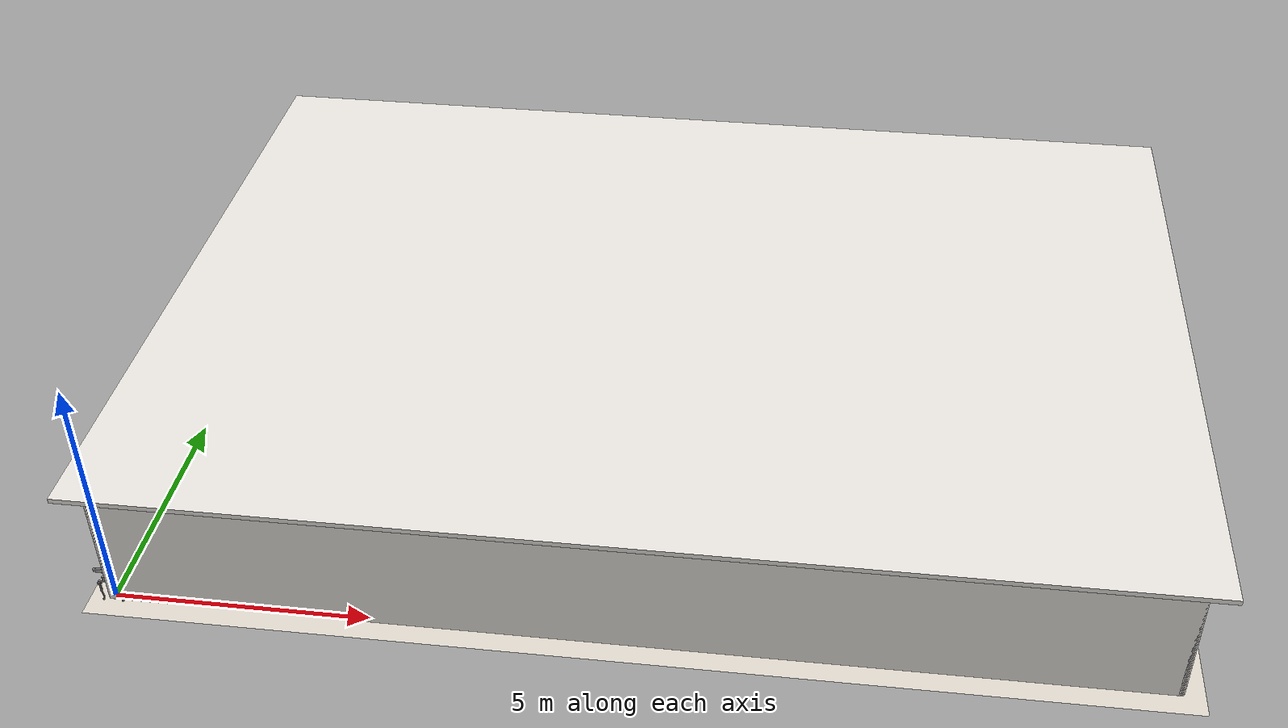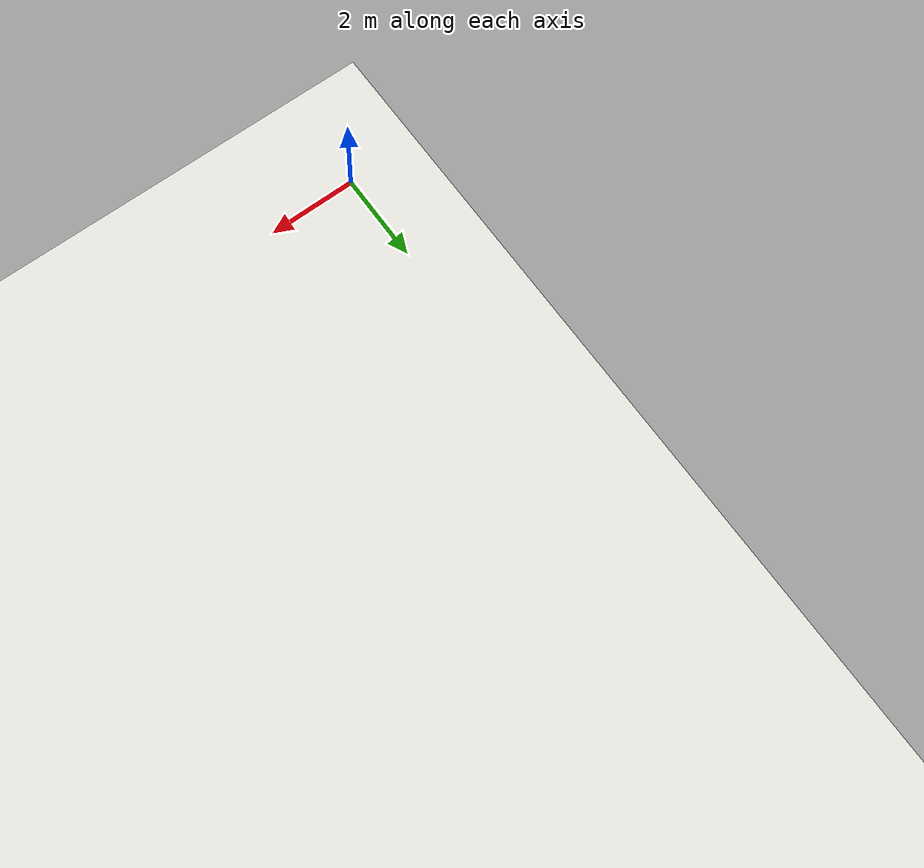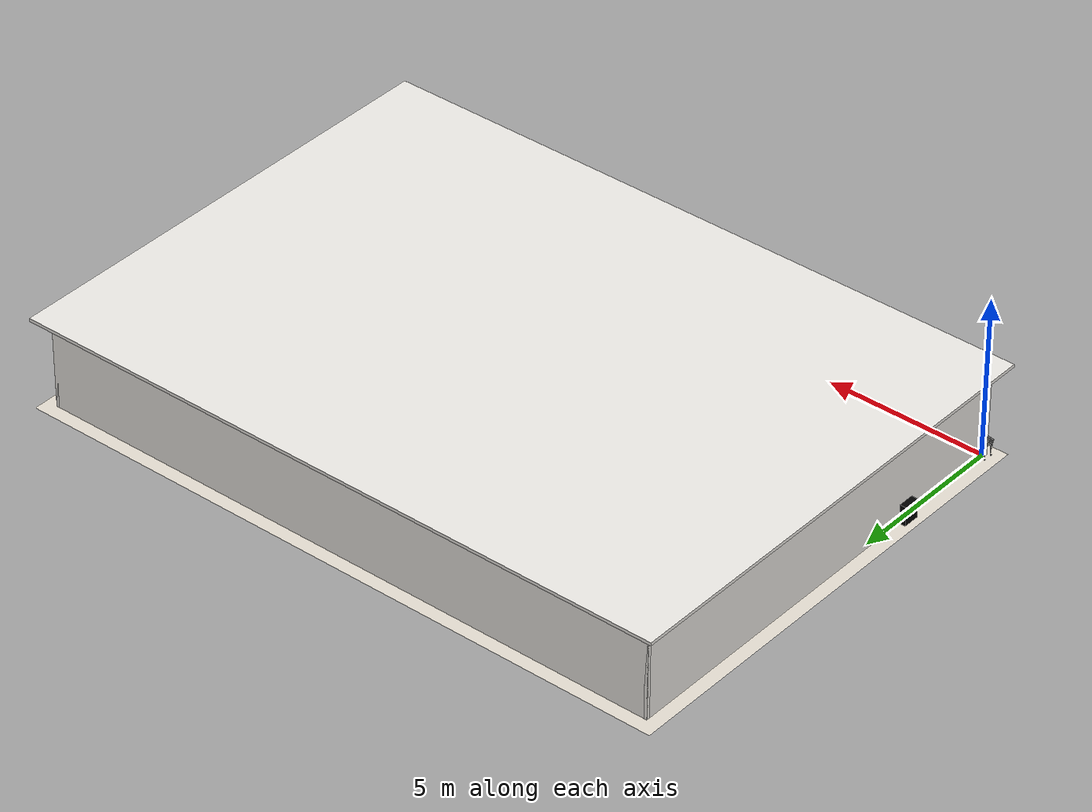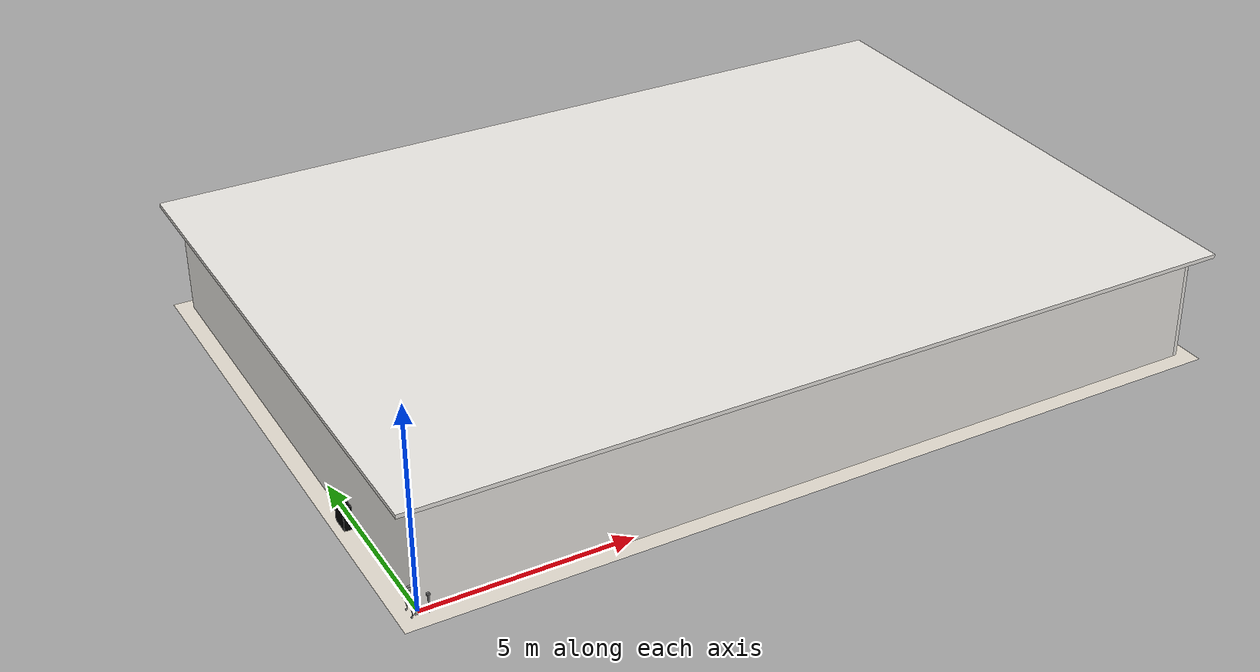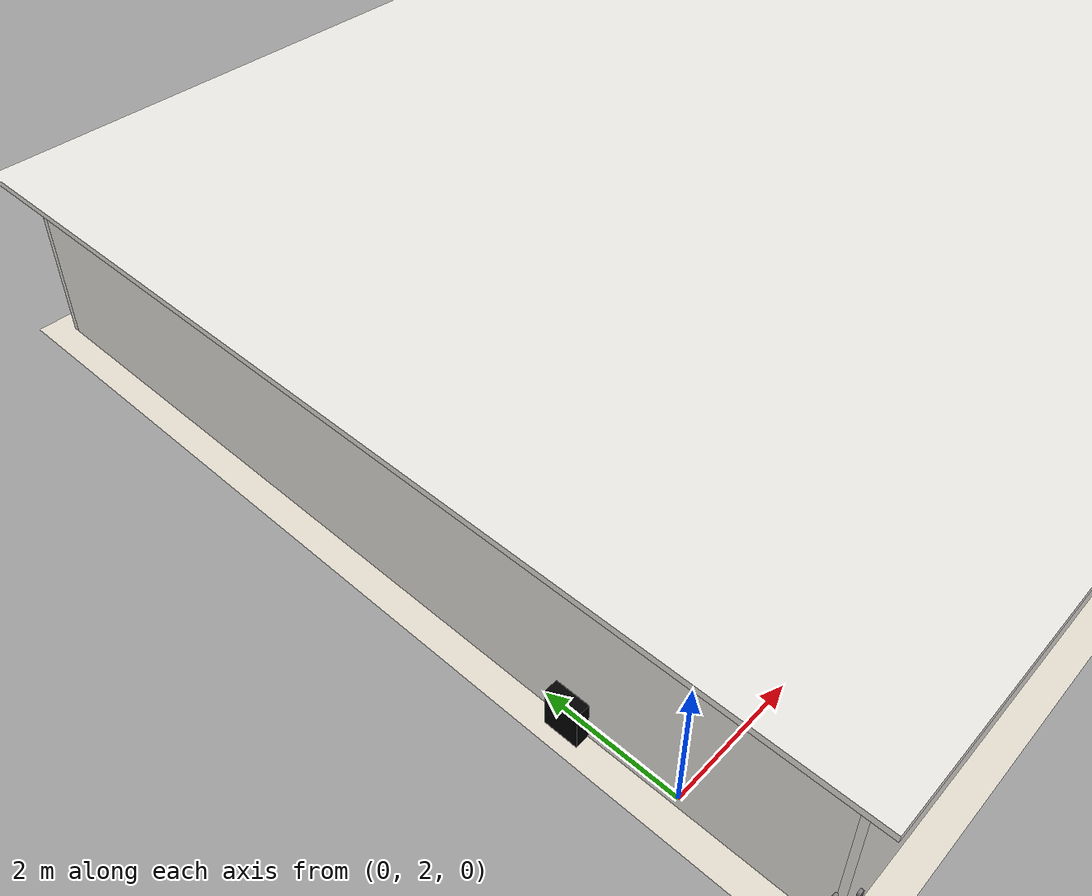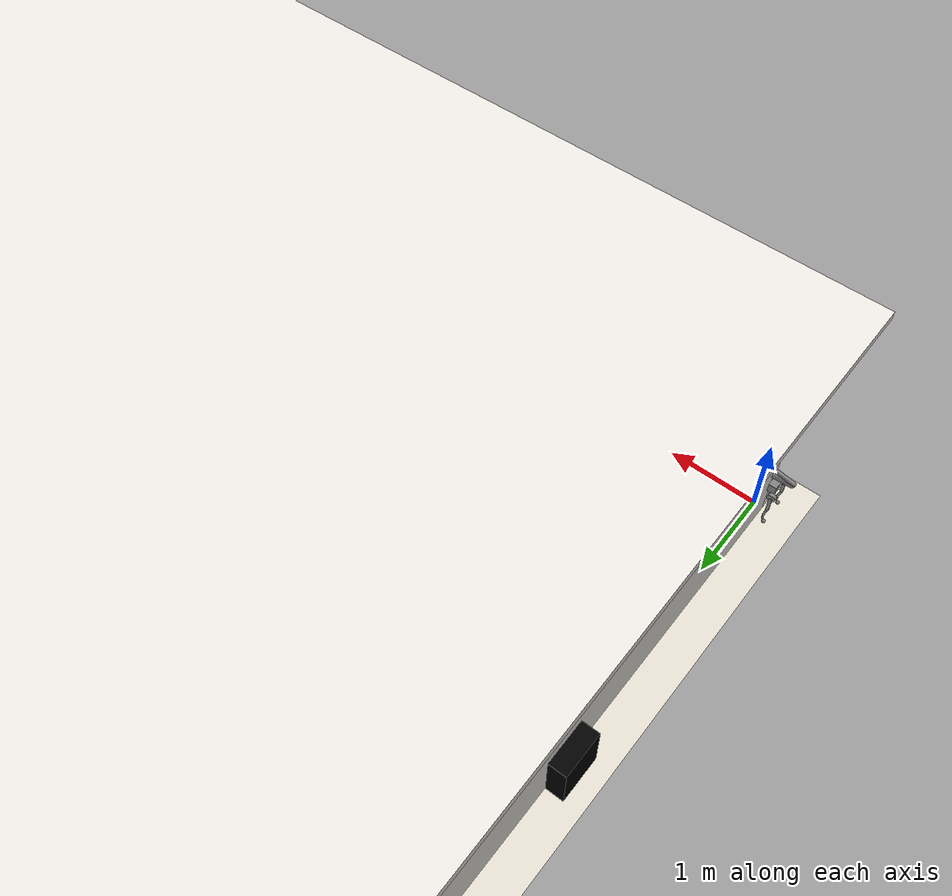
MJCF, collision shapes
<mujoco model="go2 house">
  <compiler angle="radian" meshdir="/home/yusen/Desktop/vector_os_nano/vector_os_nano/hardware/sim/mjcf/go2/assets" texturedir="/home/yusen/Desktop/vector_os_nano/vector_os_nano/hardware/sim/mjcf/go2/assets" autolimits="true"/>
  <include file="/home/yusen/Desktop/vector_os_nano/vector_os_nano/hardware/sim/mjcf/go2_piper/go2_piper.xml"/>

  <option cone="elliptic" impratio="100"/>

  <statistic center="10 7 0.5" extent="12"/>

  <visual>
    <headlight diffuse="0.5 0.5 0.5" ambient="0.4 0.4 0.4" specular="0 0 0"/>
    <rgba haze="0.15 0.25 0.35 1"/>
    <global azimuth="-120" elevation="-25" offwidth="1280" offheight="960"/>
    <map znear="0.05" zfar="50" shadowclip="0.5"/>
    <quality shadowsize="1024"/>
  </visual>

  <asset>
    <texture type="skybox" builtin="gradient" rgb1="0.88 0.90 0.95" rgb2="0.65 0.70 0.80"
             width="512" height="3072"/>

    <!-- Wall texture (subtle plaster) -->
    <texture type="2d" name="wall_tex" builtin="gradient"
             rgb1="0.94 0.93 0.91" rgb2="0.90 0.89 0.87" width="128" height="128"/>

    <!-- Floor textures -->
    <texture type="2d" name="wood_tex" builtin="checker"
             rgb1="0.78 0.68 0.48" rgb2="0.74 0.64 0.45" width="200" height="200"/>
    <texture type="2d" name="tile_tex" builtin="checker"
             rgb1="0.90 0.90 0.88" rgb2="0.80 0.80 0.78" width="150" height="150"/>
    <texture type="2d" name="carpet_tex" builtin="flat"
             rgb1="0.50 0.52 0.56" rgb2="0.45 0.47 0.51" width="100" height="100"/>
    <texture type="2d" name="marble_tex" builtin="checker"
             rgb1="0.92 0.90 0.85" rgb2="0.85 0.82 0.77" width="120" height="120"/>
    <texture type="2d" name="bath_tex" builtin="checker"
             rgb1="0.85 0.90 0.92" rgb2="0.75 0.80 0.82" width="80" height="80"/>

    <material name="wood_mat" texture="wood_tex" texuniform="true" texrepeat="10 10" reflectance="0.12"/>
    <material name="tile_mat" texture="tile_tex" texuniform="true" texrepeat="8 8" reflectance="0.25"/>
    <material name="carpet_mat" texture="carpet_tex" texuniform="true" texrepeat="3 3" reflectance="0.02"/>
    <material name="marble_mat" texture="marble_tex" texuniform="true" texrepeat="10 12" reflectance="0.2"/>
    <material name="bath_tile" texture="bath_tex" texuniform="true" texrepeat="6 6" reflectance="0.3"/>

    <material name="wall_mat" texture="wall_tex" texuniform="true" texrepeat="4 4" reflectance="0.04"/>
    <material name="accent_wall" rgba="0.82 0.85 0.90 1" reflectance="0.04"/>

    <!-- Furniture materials (used for collision boxes, some overrides) -->
    <material name="dark_wood" rgba="0.35 0.22 0.12 1" reflectance="0.12"/>
    <material name="rug_red" rgba="0.60 0.15 0.12 1" reflectance="0.02"/>
    <material name="rug_blue" rgba="0.15 0.25 0.45 1" reflectance="0.02"/>
    <material name="rug_beige" rgba="0.82 0.75 0.62 1" reflectance="0.02"/>
    <material name="painting_mat" rgba="0.85 0.65 0.40 1" reflectance="0.05"/>

    <!-- Furniture PNG textures (furniture_sim, Apache 2.0) -->
    <texture type="2d" name="tex_oak" file="furniture/wood2.png"/>
    <texture type="2d" name="tex_walnut" file="furniture/wood1.png"/>
    <texture type="2d" name="tex_cherry" file="furniture/wood4.png"/>
    <texture type="2d" name="tex_pine" file="furniture/wood0.png"/>
    <texture type="2d" name="tex_steel" file="furniture/metal0.png"/>
    <texture type="2d" name="tex_chrome" file="furniture/metal1.png"/>
    <texture type="2d" name="tex_marble" file="furniture/stone0.png"/>
    <texture type="2d" name="tex_ceramic" file="furniture/stone1.png"/>

    <!-- Textured furniture materials -->
    <material name="mat_oak" texture="tex_oak" texuniform="true" texrepeat="3 3" reflectance="0.12"/>
    <material name="mat_walnut" texture="tex_walnut" texuniform="true" texrepeat="3 3" reflectance="0.12"/>
    <material name="mat_cherry" texture="tex_cherry" texuniform="true" texrepeat="3 3" reflectance="0.10"/>
    <material name="mat_pine" texture="tex_pine" texuniform="true" texrepeat="4 4" reflectance="0.08"/>
    <material name="mat_steel" texture="tex_steel" texuniform="true" texrepeat="2 2" reflectance="0.40"/>
    <material name="mat_chrome" texture="tex_chrome" texuniform="true" texrepeat="2 2" reflectance="0.50"/>
    <material name="mat_marble" texture="tex_marble" texuniform="true" texrepeat="4 4" reflectance="0.25"/>
    <material name="mat_ceramic" texture="tex_ceramic" texuniform="true" texrepeat="3 3" reflectance="0.20"/>

    <!-- ==================== FURNITURE MESHES (Kenney CC0) ==================== -->
    <!-- Y-up OBJ → Z-up MuJoCo via euler="1.5708 0 0" on geom -->

    <!-- Sofa -->
    <mesh name="m_loungeSofa_carpet" file="furniture/loungeSofa_carpet.obj" scale="2.2 2.2 2.2" inertia="shell"/>
    <mesh name="m_loungeSofa_wood" file="furniture/loungeSofa_wood.obj" scale="2.2 2.2 2.2" inertia="shell"/>

    <!-- Coffee Table -->
    <mesh name="m_coffee_table" file="furniture/tableCoffee.obj" scale="1.8 1.8 1.8" inertia="shell"/>

    <!-- TV Console -->
    <mesh name="m_tv_console" file="furniture/cabinetTelevision.obj" scale="2.0 2.0 2.0" inertia="shell"/>

    <!-- TV -->
    <mesh name="m_televisionModern_metalDark" file="furniture/televisionModern_metalDark.obj" scale="1.7 1.7 1.7" inertia="shell"/>
    <mesh name="m_televisionModern_metal" inertia="shell" file="furniture/televisionModern_metal.obj" scale="1.7 1.7 1.7"/>

    <!-- Floor Lamp -->
    <mesh name="m_lampRoundFloor_metal" file="furniture/lampRoundFloor_metal.obj" scale="1.7 1.7 1.7" inertia="shell"/>
    <mesh name="m_lampRoundFloor_lamp" file="furniture/lampRoundFloor_lamp.obj" scale="1.7 1.7 1.7" inertia="shell"/>

    <!-- Rug -->
    <mesh name="m_rugRectangle_carpet" file="furniture/rugRectangle_carpet.obj" scale="2.0 2.0 2.0" inertia="shell"/>
    <mesh name="m_rugRectangle_carpetDarker" file="furniture/rugRectangle_carpetDarker.obj" scale="2.0 2.0 2.0" inertia="shell"/>

    <!-- Dining Table -->
    <mesh name="m_dining_table" file="furniture/table.obj" scale="2.0 2.0 2.0" inertia="shell"/>

    <!-- Chair -->
    <mesh name="m_chair" file="furniture/chair.obj" scale="2.1 2.1 2.1" inertia="shell"/>

    <!-- Potted Plant -->
    <!-- pottedPlant meshes removed — collision cylinders trap Go2 -->

    <!-- Sideboard -->
    <mesh name="m_sideTableDrawers_wood" file="furniture/sideTableDrawers_wood.obj" scale="2.0 2.0 2.0" inertia="shell"/>
    <mesh name="m_sideTableDrawers_defaultMat" inertia="shell" file="furniture/sideTableDrawers_defaultMat.obj" scale="2.0 2.0 2.0"/>
    <mesh name="m_sideTableDrawers_metal" inertia="shell" file="furniture/sideTableDrawers_metal.obj" scale="2.0 2.0 2.0"/>

    <!-- Kitchen Cabinet Drawer -->
    <mesh name="m_kitchenCabinetDrawer_metal" file="furniture/kitchenCabinetDrawer_metal.obj" scale="2.0 2.0 2.0" inertia="shell"/>
    <mesh name="m_kitchenCabinetDrawer_wood" file="furniture/kitchenCabinetDrawer_wood.obj" scale="2.0 2.0 2.0" inertia="shell"/>
    <mesh name="m_kitchenCabinetDrawer_woodDark" inertia="shell" file="furniture/kitchenCabinetDrawer_woodDark.obj" scale="2.0 2.0 2.0"/>

    <!-- Kitchen Stove -->
    <mesh name="m_kitchenStove_metal" file="furniture/kitchenStove_metal.obj" scale="2.0 2.0 2.0" inertia="shell"/>
    <mesh name="m_kitchenStove_wood" file="furniture/kitchenStove_wood.obj" scale="2.0 2.0 2.0" inertia="shell"/>
    <mesh name="m_kitchenStove_metalDark" file="furniture/kitchenStove_metalDark.obj" scale="2.0 2.0 2.0" inertia="shell"/>
    <mesh name="m_kitchenStove_carpetWhite" inertia="shell" file="furniture/kitchenStove_carpetWhite.obj" scale="2.0 2.0 2.0"/>
    <mesh name="m_kitchenStove_glass" inertia="shell" file="furniture/kitchenStove_glass.obj" scale="2.0 2.0 2.0"/>

    <!-- Fridge -->
    <mesh name="m_kitchenFridgeLarge_metalLight" file="furniture/kitchenFridgeLarge_metalLight.obj" scale="1.9 1.9 1.9" inertia="shell"/>
    <mesh name="m_kitchenFridgeLarge_metalMedium" file="furniture/kitchenFridgeLarge_metalMedium.obj" scale="1.9 1.9 1.9" inertia="shell"/>

    <!-- Bar Stool -->
    <mesh name="m_stoolBar_wood" file="furniture/stoolBar_wood.obj" scale="1.8 1.8 1.8" inertia="shell"/>
    <mesh name="m_stoolBar_carpet" file="furniture/stoolBar_carpet.obj" scale="1.8 1.8 1.8" inertia="shell"/>

    <!-- Desk -->
    <mesh name="m_desk_wood" file="furniture/desk_wood.obj" scale="2.0 2.0 2.0" inertia="shell"/>
    <mesh name="m_desk_metal" inertia="shell" file="furniture/desk_metal.obj" scale="2.0 2.0 2.0"/>

    <!-- Computer Screen -->
    <mesh name="m_computerScreen_metalDark" file="furniture/computerScreen_metalDark.obj" scale="1.6 1.6 1.6" inertia="shell"/>
    <mesh name="m_computerScreen_metal" file="furniture/computerScreen_metal.obj" scale="1.6 1.6 1.6" inertia="shell"/>

    <!-- Desk Chair -->
    <mesh name="m_chairDesk_metalMedium" file="furniture/chairDesk_metalMedium.obj" scale="1.7 1.7 1.7" inertia="shell"/>
    <mesh name="m_chairDesk_carpet" file="furniture/chairDesk_carpet.obj" scale="1.7 1.7 1.7" inertia="shell"/>

    <!-- Bookcase -->
    <mesh name="m_bookshelf" file="furniture/bookcaseOpen.obj" scale="2.0 2.0 2.0" inertia="shell"/>

    <!-- Double Bed -->
    <mesh name="m_bedDouble_carpet" file="furniture/bedDouble_carpet.obj" scale="2.0 2.0 2.0" inertia="shell"/>
    <mesh name="m_bedDouble_carpetWhite" file="furniture/bedDouble_carpetWhite.obj" scale="2.0 2.0 2.0" inertia="shell"/>
    <mesh name="m_bedDouble_metal" file="furniture/bedDouble_metal.obj" scale="2.0 2.0 2.0" inertia="shell"/>
    <mesh name="m_bedDouble_wood" file="furniture/bedDouble_wood.obj" scale="2.0 2.0 2.0" inertia="shell"/>

    <!-- Cabinet Bed Drawer (nightstand) -->
    <mesh name="m_cabinetBedDrawer_wood" file="furniture/cabinetBedDrawer_wood.obj" scale="1.9 1.9 1.9" inertia="shell"/>
    <mesh name="m_cabinetBedDrawer_defaultMat" inertia="shell" file="furniture/cabinetBedDrawer_defaultMat.obj" scale="1.9 1.9 1.9"/>
    <mesh name="m_cabinetBedDrawer_metal" file="furniture/cabinetBedDrawer_metal.obj" scale="1.9 1.9 1.9" inertia="shell"/>

    <!-- Single Bed -->
    <mesh name="m_bedSingle_carpet" file="furniture/bedSingle_carpet.obj" scale="1.7 1.7 1.7" inertia="shell"/>
    <mesh name="m_bedSingle_carpetWhite" file="furniture/bedSingle_carpetWhite.obj" scale="1.7 1.7 1.7" inertia="shell"/>
    <mesh name="m_bedSingle_metal" file="furniture/bedSingle_metal.obj" scale="1.7 1.7 1.7" inertia="shell"/>
    <mesh name="m_bedSingle_wood" file="furniture/bedSingle_wood.obj" scale="1.7 1.7 1.7" inertia="shell"/>

    <!-- Dresser (cabinetBedDrawerTable) -->
    <mesh name="m_dresser_wood" file="furniture/cabinetBedDrawerTable_wood.obj" scale="1.9 1.9 1.9" inertia="shell"/>
    <mesh name="m_dresser_defaultMat" file="furniture/cabinetBedDrawerTable_defaultMat.obj" scale="1.9 1.9 1.9" inertia="shell"/>
    <mesh name="m_dresser_metal" file="furniture/cabinetBedDrawerTable_metal.obj" scale="1.9 1.9 1.9" inertia="shell"/>

    <!-- Bathtub -->
    <mesh name="m_bathtub_carpetWhite" file="furniture/bathtub_carpetWhite.obj" scale="1.4 1.4 1.4" inertia="shell"/>
    <mesh name="m_bathtub_metalLight" file="furniture/bathtub_metalLight.obj" scale="1.4 1.4 1.4" inertia="shell"/>
    <mesh name="m_bathtub_metalDark" inertia="shell" file="furniture/bathtub_metalDark.obj" scale="1.4 1.4 1.4"/>

    <!-- Bathroom Sink (vanity) -->
    <mesh name="m_bathroomSink_defaultMat" file="furniture/bathroomSink_defaultMat.obj" scale="1.5 1.5 1.5" inertia="shell"/>
    <mesh name="m_bathroomSink_metalLight" file="furniture/bathroomSink_metalLight.obj" scale="1.5 1.5 1.5" inertia="shell"/>
    <mesh name="m_bathroomSink_carpetWhite" inertia="shell" file="furniture/bathroomSink_carpetWhite.obj" scale="1.5 1.5 1.5"/>

    <!-- Washer -->
    <mesh name="m_washer_metalLight" file="furniture/washer_metalLight.obj" scale="1.7 1.7 1.7" inertia="shell"/>
    <mesh name="m_washer_metalMedium" file="furniture/washer_metalMedium.obj" scale="1.7 1.7 1.7" inertia="shell"/>
    <mesh name="m_washer_metalDark" inertia="shell" file="furniture/washer_metalDark.obj" scale="1.7 1.7 1.7"/>
    <mesh name="m_washer_metal" file="furniture/washer_metal.obj" scale="1.7 1.7 1.7" inertia="shell"/>
    <mesh name="m_washer_glass" inertia="shell" file="furniture/washer_glass.obj" scale="1.7 1.7 1.7"/>
    <mesh name="m_washer_defaultMat" inertia="shell" file="furniture/washer_defaultMat.obj" scale="1.7 1.7 1.7"/>

    <!-- Dryer -->
    <mesh name="m_dryer_metalLight" file="furniture/dryer_metalLight.obj" scale="1.7 1.7 1.7" inertia="shell"/>
    <mesh name="m_dryer_metalMedium" file="furniture/dryer_metalMedium.obj" scale="1.7 1.7 1.7" inertia="shell"/>
    <mesh name="m_dryer_metalDark" inertia="shell" file="furniture/dryer_metalDark.obj" scale="1.7 1.7 1.7"/>

    <!-- Side Table (hallway console) -->
    <mesh name="m_sideTable_wood" file="furniture/sideTable_wood.obj" scale="1.8 1.8 1.8" inertia="shell"/>
    <mesh name="m_sideTable_defaultMat" inertia="shell" file="furniture/sideTable_defaultMat.obj" scale="1.8 1.8 1.8"/>
  </asset>

  <worldbody>
    <!-- ==================== LIGHTING ==================== -->
    <light name="light_living" pos="3 2.5 2.7" dir="0 0 -1" diffuse="0.55 0.50 0.42" cutoff="65" castshadow="false"/>
    <light name="light_dining" pos="3 7.5 2.7" dir="0 0 -1" diffuse="0.55 0.50 0.42" cutoff="65" castshadow="false"/>
    <light name="light_kitchen" pos="17 2.5 2.7" dir="0 0 -1" diffuse="0.60 0.58 0.52" cutoff="65" castshadow="false"/>
    <light name="light_study" pos="17 7.5 2.7" dir="0 0 -1" diffuse="0.55 0.52 0.45" cutoff="65" castshadow="false"/>
    <light name="light_hall_a" pos="10 3 2.7" dir="0 0 -1" diffuse="0.50 0.48 0.42" cutoff="55" castshadow="false"/>
    <light name="light_hall_b" pos="10 7 2.7" dir="0 0 -1" diffuse="0.50 0.48 0.42" cutoff="55" castshadow="false"/>
    <light name="light_master" pos="3.5 12 2.7" dir="0 0 -1" diffuse="0.50 0.45 0.38" cutoff="60" castshadow="false"/>
    <light name="light_guest" pos="16 12 2.7" dir="0 0 -1" diffuse="0.50 0.45 0.38" cutoff="60" castshadow="false"/>
    <light name="light_bath" pos="8.5 12 2.7" dir="0 0 -1" diffuse="0.55 0.55 0.55" cutoff="55" castshadow="false"/>
    <light name="sun" pos="10 7 4" dir="0 0 -1" directional="true" diffuse="0.35 0.35 0.35"/><!-- sun only shadow caster -->
    <light name="fill_hall" pos="10 5 0.5" dir="0 0 1" diffuse="0.15 0.14 0.12" castshadow="false"/>
    <light name="fill_living" pos="3 2.5 0.5" dir="0 0 1" diffuse="0.12 0.11 0.10" castshadow="false"/>
    <light name="fill_dining" pos="3 7.5 0.5" dir="0 0 1" diffuse="0.12 0.11 0.10" castshadow="false"/>
    <light name="fill_kitchen" pos="17 2.5 0.5" dir="0 0 1" diffuse="0.14 0.14 0.12" castshadow="false"/>

    <!-- ==================== FLOORS ==================== -->
    <geom name="floor" type="plane" pos="10 7 0" size="10.5 7.5 0.05" material="marble_mat"/>
    <geom name="floor_raycast" type="box" pos="10 7 -0.02" size="10.5 7.5 0.01"
          contype="0" conaffinity="0" group="3" rgba="0 0 0 0"/>
    <geom name="ceiling" type="box" pos="10 7 2.85" size="10.5 7.5 0.05" material="wall_mat"
          contype="0" conaffinity="0" group="3"/>
    <geom name="f_living" type="box" pos="3 2.5 0.001" size="3 2.5 0.001" material="wood_mat" contype="0" conaffinity="0"/>
    <geom name="f_dining" type="box" pos="3 7.5 0.001" size="3 2.5 0.001" material="wood_mat" contype="0" conaffinity="0"/>
    <geom name="f_kitchen" type="box" pos="17 2.5 0.001" size="3 2.5 0.001" material="tile_mat" contype="0" conaffinity="0"/>
    <geom name="f_study" type="box" pos="17 7.5 0.001" size="3 2.5 0.001" material="wood_mat" contype="0" conaffinity="0"/>
    <geom name="f_master" type="box" pos="3.5 12 0.001" size="3.5 2 0.001" material="carpet_mat" contype="0" conaffinity="0"/>
    <geom name="f_guest" type="box" pos="16 12 0.001" size="4 2 0.001" material="carpet_mat" contype="0" conaffinity="0"/>
    <geom name="f_bath" type="box" pos="8.5 12 0.001" size="1.5 2 0.001" material="bath_tile" contype="0" conaffinity="0"/>

    <!-- ==================== EXTERIOR WALLS ==================== -->
    <geom name="ew_south" type="box" pos="10 -0.05 1.4" size="10.1 0.05 1.4" material="wall_mat"/>
    <geom name="ew_north" type="box" pos="10 14.05 1.4" size="10.1 0.05 1.4" material="wall_mat"/>
    <geom name="ew_west" type="box" pos="-0.05 7 1.4" size="0.05 7.1 1.4" material="wall_mat"/>
    <geom name="ew_east" type="box" pos="20.05 7 1.4" size="0.05 7.1 1.4" material="wall_mat"/>

    <!-- ==================== INTERIOR WALLS ==================== -->
    <geom name="iw_l1" type="box" pos="6 1.2 1.4" size="0.05 1.2 1.4" material="accent_wall"/>
    <geom name="iw_l2" type="box" pos="6 4.3 1.4" size="0.05 0.7 1.4" material="accent_wall"/>
    <geom name="iw_l3" type="box" pos="6 6.2 1.4" size="0.05 1.2 1.4" material="accent_wall"/>
    <geom name="iw_l4" type="box" pos="6 9.3 1.4" size="0.05 0.7 1.4" material="accent_wall"/>
    <geom name="iw_r1" type="box" pos="14 1.2 1.4" size="0.05 1.2 1.4" material="accent_wall"/>
    <geom name="iw_r2" type="box" pos="14 4.3 1.4" size="0.05 0.7 1.4" material="accent_wall"/>
    <geom name="iw_r3" type="box" pos="14 6.2 1.4" size="0.05 1.2 1.4" material="accent_wall"/>
    <geom name="iw_r4" type="box" pos="14 9.3 1.4" size="0.05 0.7 1.4" material="accent_wall"/>
    <geom name="iw_ld1" type="box" pos="1.2 5 1.4" size="1.2 0.05 1.4" material="accent_wall"/>
    <geom name="iw_ld2" type="box" pos="4.8 5 1.4" size="1.2 0.05 1.4" material="accent_wall"/>
    <geom name="iw_ks1" type="box" pos="15.2 5 1.4" size="1.2 0.05 1.4" material="accent_wall"/>
    <geom name="iw_ks2" type="box" pos="18.8 5 1.4" size="1.2 0.05 1.4" material="accent_wall"/>
    <geom name="iw_b1" type="box" pos="1.2 10 1.4" size="1.2 0.05 1.4" material="wall_mat"/>
    <geom name="iw_b2" type="box" pos="4.8 10 1.4" size="1.2 0.05 1.4" material="wall_mat"/>
    <geom name="iw_b3" type="box" pos="6.95 10 1.4" size="0.95 0.05 1.4" material="wall_mat"/>
    <geom name="iw_b4" type="box" pos="10.55 10 1.4" size="1.45 0.05 1.4" material="wall_mat"/><!-- sealed laundry door -->
    <geom name="iw_b5" type="box" pos="13.0 10 1.4" size="1.0 0.05 1.4" material="wall_mat"/>
    <geom name="iw_b6" type="box" pos="14.7 10 1.4" size="0.7 0.05 1.4" material="wall_mat"/>
    <geom name="iw_b7" type="box" pos="18.3 10 1.4" size="1.7 0.05 1.4" material="wall_mat"/>
    <geom name="iw_bath_w" type="box" pos="7 12 1.4" size="0.05 2.05 1.4" material="wall_mat"/>
    <!-- iw_bath_e REMOVED — bathroom + laundry merged into one room -->
    <geom name="iw_laund_e" type="box" pos="12 12 1.4" size="0.05 2.05 1.4" material="wall_mat"/>

    <!-- ==================== LIVING ROOM (x=0..6, y=0..5) ==================== -->

    <body name="sofa_main" pos="1.8 1.0 0">
      <geom type="mesh" mesh="m_loungeSofa_carpet" euler="1.5708 0 0" pos="1.08 0.45 0" rgba="0.94 0.37 0.34 1" contype="0" conaffinity="0"/>
      <geom type="mesh" mesh="m_loungeSofa_wood" euler="1.5708 0 0" pos="1.08 0.45 0" material="mat_walnut" contype="0" conaffinity="0"/>
      <geom type="box" pos="0 0 0.45" size="1.1 0.45 0.45" rgba="0 0 0 0" group="3"/>
    </body>

    <body name="coffee_tbl" pos="1.8 2.3 0">
      <geom type="mesh" mesh="m_coffee_table" euler="1.5708 0 0" pos="-0.24 0.18 0" rgba="0.90 0.60 0.39 1" contype="0" conaffinity="0"/>
      <geom type="box" pos="0 0 0.20" size="0.6 0.35 0.20" rgba="0 0 0 0" group="3"/>
    </body>

    <body name="tv_console" pos="0.5 3.5 0">
      <geom type="mesh" mesh="m_tv_console" euler="1.5708 0 0" pos="0.80 0.25 0" rgba="0.90 0.60 0.39 1" contype="0" conaffinity="0"/>
      <geom type="box" pos="0 0 0.30" size="0.8 0.25 0.30" rgba="0 0 0 0" group="3"/>
    </body>

    <body name="tv_screen" pos="0.5 3.5 0.62">
      <geom type="mesh" mesh="m_televisionModern_metalDark" euler="1.5708 0 0" rgba="0.31 0.39 0.39 1" contype="0" conaffinity="0"/>
      <geom type="mesh" mesh="m_televisionModern_metal" euler="1.5708 0 0" rgba="0.74 0.82 0.84 1" contype="0" conaffinity="0"/>
    </body>

    <body name="lamp_living" pos="0.4 4.2 0">
      <geom type="mesh" mesh="m_lampRoundFloor_metal" euler="1.5708 0 0" pos="0.10 0.10 0" material="mat_chrome" contype="0" conaffinity="0"/>
      <geom type="mesh" mesh="m_lampRoundFloor_lamp" euler="1.5708 0 0" pos="0.10 0.10 0" rgba="1.0 0.91 0.59 1" contype="0" conaffinity="0"/>
      <geom type="cylinder" pos="0 0 0.7" size="0.12 0.7" rgba="0 0 0 0" group="3"/>
    </body>

    <geom name="rug_living_carpet" type="mesh" mesh="m_rugRectangle_carpet" euler="1.5708 0 0" pos="2.0 2.0 0.005"
          rgba="0.94 0.37 0.34 1" contype="0" conaffinity="0"/>
    <geom name="rug_living_darker" type="mesh" mesh="m_rugRectangle_carpetDarker" euler="1.5708 0 0" pos="2.0 2.0 0.005"
          rgba="0.61 0.30 0.29 1" contype="0" conaffinity="0"/>

    <geom name="art_living" type="box" pos="0.02 2.5 1.5" size="0.02 0.4 0.3"
          material="painting_mat" contype="0" conaffinity="0"/>

    <!-- ==================== DINING ROOM (x=0..6, y=5..10) ==================== -->

    <body name="dining_table" pos="3 7.5 0">
      <geom type="mesh" mesh="m_dining_table" euler="1.5708 0 0" pos="0.84 0.45 0" rgba="0.90 0.60 0.39 1" contype="0" conaffinity="0"/>
      <geom type="box" pos="0 0 0.33" size="0.84 0.45 0.33" rgba="0 0 0 0" group="3"/>
    </body>

    <body name="dchair1" pos="2.0 7.5 0">
      <geom type="mesh" mesh="m_chair" euler="1.5708 0 0" pos="0.21 0.21 0" material="mat_oak" contype="0" conaffinity="0"/>
      <geom type="box" pos="0 0 0.45" size="0.21 0.21 0.45" rgba="0 0 0 0" group="3"/>
    </body>
    <body name="dchair2" pos="4.0 7.5 0">
      <geom type="mesh" mesh="m_chair" euler="1.5708 0 3.1416" pos="-0.21 -0.21 0" material="mat_oak" contype="0" conaffinity="0"/>
      <geom type="box" pos="0 0 0.45" size="0.21 0.21 0.45" rgba="0 0 0 0" group="3"/>
    </body>
    <body name="dchair3" pos="3.0 6.7 0">
      <geom type="mesh" mesh="m_chair" euler="1.5708 0 1.5708" pos="0.21 -0.21 0" material="mat_oak" contype="0" conaffinity="0"/>
      <geom type="box" pos="0 0 0.45" size="0.21 0.21 0.45" rgba="0 0 0 0" group="3"/>
    </body>
    <body name="dchair4" pos="3.0 8.3 0">
      <geom type="mesh" mesh="m_chair" euler="1.5708 0 -1.5708" pos="-0.21 0.21 0" material="mat_oak" contype="0" conaffinity="0"/>
      <geom type="box" pos="0 0 0.45" size="0.21 0.21 0.45" rgba="0 0 0 0" group="3"/>
    </body>

    <body name="sideboard" pos="0.5 8.5 0">
      <geom type="mesh" mesh="m_sideTableDrawers_wood" euler="1.5708 0 0" pos="0.51 0.20 0" material="mat_cherry" contype="0" conaffinity="0"/>
      <geom type="mesh" mesh="m_sideTableDrawers_defaultMat" euler="1.5708 0 0" pos="0.51 0.20 0" rgba="1.0 1.0 1.0 1" contype="0" conaffinity="0"/>
      <geom type="mesh" mesh="m_sideTableDrawers_metal" euler="1.5708 0 0" pos="0.51 0.20 0" rgba="0.74 0.82 0.84 1" contype="0" conaffinity="0"/>
      <geom type="box" pos="0 0 0.38" size="0.53 0.22 0.38" rgba="0 0 0 0" group="3"/>
    </body>

    <!-- plant_dining REMOVED — collision cylinder traps Go2 -->

    <!-- ==================== KITCHEN (x=14..20, y=0..5) ==================== -->

    <body name="counter_east" pos="19.2 1.0 0">
      <geom type="mesh" mesh="m_kitchenCabinetDrawer_metal" euler="1.5708 0 0" pos="0.43 0.45 0" material="mat_chrome" contype="0" conaffinity="0"/>
      <geom type="mesh" mesh="m_kitchenCabinetDrawer_wood" euler="1.5708 0 0" pos="0.43 0.45 0" material="mat_cherry" contype="0" conaffinity="0"/>
      <geom type="mesh" mesh="m_kitchenCabinetDrawer_woodDark" euler="1.5708 0 0" pos="0.43 0.45 0" material="mat_walnut" contype="0" conaffinity="0"/>
      <geom type="box" pos="0 0 0.45" size="0.43 0.45 0.45" rgba="0 0 0 0" group="3"/>
    </body>
    <body name="counter_east2" pos="19.2 2.0 0">
      <geom type="mesh" mesh="m_kitchenCabinetDrawer_metal" euler="1.5708 0 0" pos="0.43 0.45 0" material="mat_chrome" contype="0" conaffinity="0"/>
      <geom type="mesh" mesh="m_kitchenCabinetDrawer_wood" euler="1.5708 0 0" pos="0.43 0.45 0" material="mat_cherry" contype="0" conaffinity="0"/>
      <geom type="mesh" mesh="m_kitchenCabinetDrawer_woodDark" euler="1.5708 0 0" pos="0.43 0.45 0" material="mat_walnut" contype="0" conaffinity="0"/>
      <geom type="box" pos="0 0 0.45" size="0.43 0.45 0.45" rgba="0 0 0 0" group="3"/>
    </body>
    <body name="counter_east3" pos="19.2 3.0 0">
      <geom type="mesh" mesh="m_kitchenCabinetDrawer_metal" euler="1.5708 0 0" pos="0.43 0.45 0" material="mat_chrome" contype="0" conaffinity="0"/>
      <geom type="mesh" mesh="m_kitchenCabinetDrawer_wood" euler="1.5708 0 0" pos="0.43 0.45 0" material="mat_cherry" contype="0" conaffinity="0"/>
      <geom type="mesh" mesh="m_kitchenCabinetDrawer_woodDark" euler="1.5708 0 0" pos="0.43 0.45 0" material="mat_walnut" contype="0" conaffinity="0"/>
      <geom type="box" pos="0 0 0.45" size="0.43 0.45 0.45" rgba="0 0 0 0" group="3"/>
    </body>

    <body name="counter_south" pos="15.5 0.5 0">
      <geom type="mesh" mesh="m_kitchenStove_metal" euler="1.5708 0 0" pos="0.43 0.45 0" material="mat_steel" contype="0" conaffinity="0"/>
      <geom type="mesh" mesh="m_kitchenStove_wood" euler="1.5708 0 0" pos="0.43 0.45 0" material="mat_cherry" contype="0" conaffinity="0"/>
      <geom type="mesh" mesh="m_kitchenStove_metalDark" euler="1.5708 0 0" pos="0.43 0.45 0" rgba="0.31 0.39 0.39 1" contype="0" conaffinity="0"/>
      <geom type="mesh" mesh="m_kitchenStove_carpetWhite" euler="1.5708 0 0" pos="0.43 0.45 0" rgba="0.97 1.0 1.0 1" contype="0" conaffinity="0"/>
      <geom type="mesh" mesh="m_kitchenStove_glass" euler="1.5708 0 0" pos="0.43 0.45 0" rgba="0.70 0.83 0.77 1" contype="0" conaffinity="0"/>
      <geom type="box" pos="0 0 0.45" size="0.43 0.45 0.45" rgba="0 0 0 0" group="3"/>
    </body>

    <body name="counter_south2" pos="16.5 0.5 0">
      <geom type="mesh" mesh="m_kitchenCabinetDrawer_metal" euler="1.5708 0 0" pos="0.43 0.45 0" material="mat_chrome" contype="0" conaffinity="0"/>
      <geom type="mesh" mesh="m_kitchenCabinetDrawer_wood" euler="1.5708 0 0" pos="0.43 0.45 0" material="mat_cherry" contype="0" conaffinity="0"/>
      <geom type="mesh" mesh="m_kitchenCabinetDrawer_woodDark" euler="1.5708 0 0" pos="0.43 0.45 0" material="mat_walnut" contype="0" conaffinity="0"/>
      <geom type="box" pos="0 0 0.45" size="0.43 0.45 0.45" rgba="0 0 0 0" group="3"/>
    </body>

    <body name="island" pos="17 2.8 0">
      <geom type="mesh" mesh="m_kitchenCabinetDrawer_metal" euler="1.5708 0 1.5708" pos="0.45 -0.43 0" material="mat_chrome" contype="0" conaffinity="0"/>
      <geom type="mesh" mesh="m_kitchenCabinetDrawer_wood" euler="1.5708 0 1.5708" pos="0.45 -0.43 0" material="mat_cherry" contype="0" conaffinity="0"/>
      <geom type="mesh" mesh="m_kitchenCabinetDrawer_woodDark" euler="1.5708 0 1.5708" pos="0.45 -0.43 0" material="mat_walnut" contype="0" conaffinity="0"/>
      <geom type="box" pos="0 0 0.45" size="0.43 0.45 0.45" rgba="0 0 0 0" group="3"/>
    </body>

    <body name="fridge" pos="19.2 4.3 0">
      <geom type="mesh" mesh="m_kitchenFridgeLarge_metalLight" euler="1.5708 0 0" pos="0.49 0.26 0" material="mat_steel" contype="0" conaffinity="0"/>
      <geom type="mesh" mesh="m_kitchenFridgeLarge_metalMedium" euler="1.5708 0 0" pos="0.49 0.26 0" material="mat_chrome" contype="0" conaffinity="0"/>
      <geom type="box" pos="0 0 0.88" size="0.5 0.38 0.88" rgba="0 0 0 0" group="3"/>
    </body>

    <body name="stool1" pos="16.0 2.8 0">
      <geom type="mesh" mesh="m_stoolBar_wood" euler="1.5708 0 0" pos="0.24 0.21 0" material="mat_oak" contype="0" conaffinity="0"/>
      <geom type="mesh" mesh="m_stoolBar_carpet" euler="1.5708 0 0" pos="0.24 0.21 0" rgba="0.94 0.37 0.34 1" contype="0" conaffinity="0"/>
      <geom type="cylinder" pos="0 0 0.38" size="0.17 0.38" rgba="0 0 0 0" group="3"/>
    </body>
    <body name="stool2" pos="18.0 2.8 0">
      <geom type="mesh" mesh="m_stoolBar_wood" euler="1.5708 0 0" pos="0.24 0.21 0" material="mat_oak" contype="0" conaffinity="0"/>
      <geom type="mesh" mesh="m_stoolBar_carpet" euler="1.5708 0 0" pos="0.24 0.21 0" rgba="0.94 0.37 0.34 1" contype="0" conaffinity="0"/>
      <geom type="cylinder" pos="0 0 0.38" size="0.17 0.38" rgba="0 0 0 0" group="3"/>
    </body>

    <!-- ==================== STUDY (x=14..20, y=5..10) ==================== -->

    <body name="desk" pos="19.0 7.5 0">
      <geom type="mesh" mesh="m_desk_wood" euler="1.5708 0 0" pos="0.71 0.37 0" material="mat_walnut" contype="0" conaffinity="0"/>
      <geom type="mesh" mesh="m_desk_metal" euler="1.5708 0 0" pos="0.71 0.37 0" material="mat_chrome" contype="0" conaffinity="0"/>
      <geom type="box" pos="0 0 0.38" size="0.73 0.39 0.38" rgba="0 0 0 0" group="3"/>
    </body>

    <body name="monitor" pos="19.0 7.5 0.77">
      <geom type="mesh" mesh="m_computerScreen_metalDark" euler="1.5708 0 0" pos="0.31 0.08 0" rgba="0.31 0.39 0.39 1" contype="0" conaffinity="0"/>
      <geom type="mesh" mesh="m_computerScreen_metal" euler="1.5708 0 0" pos="0.31 0.08 0" rgba="0.74 0.82 0.84 1" contype="0" conaffinity="0"/>
    </body>

    <body name="desk_chair" pos="18.0 7.5 0">
      <geom type="mesh" mesh="m_chairDesk_metalMedium" euler="1.5708 0 0" pos="0.28 0.27 0" material="mat_chrome" contype="0" conaffinity="0"/>
      <geom type="mesh" mesh="m_chairDesk_carpet" euler="1.5708 0 0" pos="0.28 0.27 0" rgba="0.94 0.37 0.34 1" contype="0" conaffinity="0"/>
      <geom type="box" pos="0 0 0.50" size="0.28 0.27 0.50" rgba="0 0 0 0" group="3"/>
    </body>

    <body name="bookshelf" pos="17 5.3 0">
      <geom type="mesh" mesh="m_bookshelf" euler="1.5708 0 0" pos="0.40 0.25 0" rgba="0.90 0.60 0.39 1" contype="0" conaffinity="0"/>
      <geom type="box" pos="0 0 0.88" size="0.40 0.25 0.88" rgba="0 0 0 0" group="3"/>
    </body>

    <geom name="rug_study_carpet" type="mesh" mesh="m_rugRectangle_carpet" euler="1.5708 0 0" pos="17.5 7.5 0.005"
          rgba="0.94 0.37 0.34 1" contype="0" conaffinity="0"/>
    <geom name="rug_study_darker" type="mesh" mesh="m_rugRectangle_carpetDarker" euler="1.5708 0 0" pos="17.5 7.5 0.005"
          rgba="0.61 0.30 0.29 1" contype="0" conaffinity="0"/>

    <!-- plant_study REMOVED — collision cylinder traps Go2 -->

    <!-- ==================== MASTER BEDROOM (x=0..7, y=10..14) ==================== -->

    <body name="master_bed" pos="1.5 12 0">
      <geom type="mesh" mesh="m_bedDouble_carpet" euler="1.5708 0 0" pos="0.96 1.12 0" rgba="0.94 0.37 0.34 1" contype="0" conaffinity="0"/>
      <geom type="mesh" mesh="m_bedDouble_carpetWhite" euler="1.5708 0 0" pos="0.96 1.12 0" rgba="0.97 1.0 1.0 1" contype="0" conaffinity="0"/>
      <geom type="mesh" mesh="m_bedDouble_metal" euler="1.5708 0 0" pos="0.96 1.12 0" material="mat_chrome" contype="0" conaffinity="0"/>
      <geom type="mesh" mesh="m_bedDouble_wood" euler="1.5708 0 0" pos="0.96 1.12 0" material="mat_walnut" contype="0" conaffinity="0"/>
      <geom type="box" pos="0 0 0.35" size="0.96 1.12 0.35" rgba="0 0 0 0" group="3"/>
    </body>

    <body name="nightstand_l" pos="1.5 10.6 0">
      <geom type="mesh" mesh="m_cabinetBedDrawer_wood" euler="1.5708 0 0" pos="0.23 0.18 0" material="mat_walnut" contype="0" conaffinity="0"/>
      <geom type="mesh" mesh="m_cabinetBedDrawer_defaultMat" euler="1.5708 0 0" pos="0.23 0.18 0" rgba="1.0 1.0 1.0 1" contype="0" conaffinity="0"/>
      <geom type="mesh" mesh="m_cabinetBedDrawer_metal" euler="1.5708 0 0" pos="0.23 0.18 0" material="mat_chrome" contype="0" conaffinity="0"/>
      <geom type="box" pos="0 0 0.25" size="0.25 0.20 0.25" rgba="0 0 0 0" group="3"/>
    </body>
    <body name="nightstand_r" pos="1.5 13.4 0">
      <geom type="mesh" mesh="m_cabinetBedDrawer_wood" euler="1.5708 0 0" pos="0.23 0.18 0" material="mat_walnut" contype="0" conaffinity="0"/>
      <geom type="mesh" mesh="m_cabinetBedDrawer_defaultMat" euler="1.5708 0 0" pos="0.23 0.18 0" rgba="1.0 1.0 1.0 1" contype="0" conaffinity="0"/>
      <geom type="mesh" mesh="m_cabinetBedDrawer_metal" euler="1.5708 0 0" pos="0.23 0.18 0" material="mat_chrome" contype="0" conaffinity="0"/>
      <geom type="box" pos="0 0 0.25" size="0.25 0.20 0.25" rgba="0 0 0 0" group="3"/>
    </body>

    <body name="wardrobe" pos="5.5 13.3 0">
      <geom type="mesh" mesh="m_bookshelf" euler="1.5708 0 0" pos="0.40 0.25 0" rgba="0.90 0.60 0.39 1" contype="0" conaffinity="0"/>
      <geom type="box" pos="0 0 0.88" size="0.40 0.30 0.88" rgba="0 0 0 0" group="3"/>
    </body>

    <geom name="rug_master_carpet" type="mesh" mesh="m_rugRectangle_carpet" euler="1.5708 0 0" pos="3 12 0.005"
          rgba="0.94 0.37 0.34 1" contype="0" conaffinity="0"/>
    <geom name="rug_master_darker" type="mesh" mesh="m_rugRectangle_carpetDarker" euler="1.5708 0 0" pos="3 12 0.005"
          rgba="0.61 0.30 0.29 1" contype="0" conaffinity="0"/>

    <!-- ==================== GUEST BEDROOM (x=12..20, y=10..14) ==================== -->

    <body name="guest_bed" pos="17.5 12 0">
      <geom type="mesh" mesh="m_bedSingle_carpet" euler="1.5708 0 0" pos="1.14 0.96 0" rgba="0.94 0.37 0.34 1" contype="0" conaffinity="0"/>
      <geom type="mesh" mesh="m_bedSingle_carpetWhite" euler="1.5708 0 0" pos="1.14 0.96 0" rgba="0.97 1.0 1.0 1" contype="0" conaffinity="0"/>
      <geom type="mesh" mesh="m_bedSingle_metal" euler="1.5708 0 0" pos="1.14 0.96 0" material="mat_chrome" contype="0" conaffinity="0"/>
      <geom type="mesh" mesh="m_bedSingle_wood" euler="1.5708 0 0" pos="1.14 0.96 0" material="mat_oak" contype="0" conaffinity="0"/>
      <geom type="box" pos="0 0 0.32" size="0.5 0.96 0.32" rgba="0 0 0 0" group="3"/>
    </body>

    <body name="guest_nightstand" pos="16.3 12.5 0">
      <geom type="mesh" mesh="m_cabinetBedDrawer_wood" euler="1.5708 0 0" pos="0.23 0.18 0" material="mat_walnut" contype="0" conaffinity="0"/>
      <geom type="mesh" mesh="m_cabinetBedDrawer_defaultMat" euler="1.5708 0 0" pos="0.23 0.18 0" rgba="1.0 1.0 1.0 1" contype="0" conaffinity="0"/>
      <geom type="mesh" mesh="m_cabinetBedDrawer_metal" euler="1.5708 0 0" pos="0.23 0.18 0" material="mat_chrome" contype="0" conaffinity="0"/>
      <geom type="box" pos="0 0 0.25" size="0.25 0.20 0.25" rgba="0 0 0 0" group="3"/>
    </body>

    <body name="dresser" pos="13 13.3 0">
      <geom type="mesh" mesh="m_dresser_wood" euler="1.5708 0 0" pos="0.23 0.18 0" rgba="0.90 0.60 0.39 1" contype="0" conaffinity="0"/>
      <geom type="mesh" mesh="m_dresser_defaultMat" euler="1.5708 0 0" pos="0.23 0.18 0" rgba="1.0 1.0 1.0 1" contype="0" conaffinity="0"/>
      <geom type="mesh" mesh="m_dresser_metal" euler="1.5708 0 0" pos="0.23 0.18 0" rgba="0.74 0.82 0.84 1" contype="0" conaffinity="0"/>
      <geom type="box" pos="0 0 0.25" size="0.25 0.20 0.25" rgba="0 0 0 0" group="3"/>
    </body>

    <!-- ==================== BATHROOM (x=7..10, y=10..14) ==================== -->

    <body name="bathtub" pos="8.5 13.2 0">
      <geom type="mesh" mesh="m_bathtub_carpetWhite" euler="1.5708 0 0" pos="0.83 0.39 0" material="mat_ceramic" contype="0" conaffinity="0"/>
      <geom type="mesh" mesh="m_bathtub_metalLight" euler="1.5708 0 0" pos="0.83 0.39 0" material="mat_ceramic" contype="0" conaffinity="0"/>
      <geom type="mesh" mesh="m_bathtub_metalDark" euler="1.5708 0 0" pos="0.83 0.39 0" rgba="0.31 0.39 0.39 1" contype="0" conaffinity="0"/>
      <geom type="box" pos="0 0 0.30" size="0.83 0.39 0.30" rgba="0 0 0 0" group="3"/>
    </body>

    <body name="vanity" pos="7.5 11 0">
      <geom type="mesh" mesh="m_bathroomSink_defaultMat" euler="1.5708 0 0" pos="0.26 0.22 0" material="mat_ceramic" contype="0" conaffinity="0"/>
      <geom type="mesh" mesh="m_bathroomSink_metalLight" euler="1.5708 0 0" pos="0.26 0.22 0" material="mat_chrome" contype="0" conaffinity="0"/>
      <geom type="mesh" mesh="m_bathroomSink_carpetWhite" euler="1.5708 0 0" pos="0.26 0.22 0" material="mat_ceramic" contype="0" conaffinity="0"/>
      <geom type="box" pos="0 0 0.42" size="0.26 0.22 0.42" rgba="0 0 0 0" group="3"/>
    </body>

    <!-- ==================== LAUNDRY (merged into bathroom, x=7..12, y=10..14) ==================== -->

    <body name="washer" pos="11 11 0">
      <geom type="mesh" mesh="m_washer_metalLight" euler="1.5708 0 0" pos="0.33 0.26 0" material="mat_steel" contype="0" conaffinity="0"/>
      <geom type="mesh" mesh="m_washer_metalMedium" euler="1.5708 0 0" pos="0.33 0.26 0" material="mat_chrome" contype="0" conaffinity="0"/>
      <geom type="mesh" mesh="m_washer_metalDark" euler="1.5708 0 0" pos="0.33 0.26 0" rgba="0.31 0.39 0.39 1" contype="0" conaffinity="0"/>
      <geom type="mesh" mesh="m_washer_metal" euler="1.5708 0 0" pos="0.33 0.26 0" material="mat_chrome" contype="0" conaffinity="0"/>
      <geom type="mesh" mesh="m_washer_glass" euler="1.5708 0 0" pos="0.33 0.26 0" rgba="0.70 0.83 0.77 1" contype="0" conaffinity="0"/>
      <geom type="mesh" mesh="m_washer_defaultMat" euler="1.5708 0 0" pos="0.33 0.26 0" rgba="1.0 1.0 1.0 1" contype="0" conaffinity="0"/>
      <geom type="box" pos="0 0 0.40" size="0.33 0.33 0.40" rgba="0 0 0 0" group="3"/>
    </body>
    <body name="dryer_unit" pos="11 12 0">
      <geom type="mesh" mesh="m_dryer_metalLight" euler="1.5708 0 0" pos="0.33 0.27 0" material="mat_steel" contype="0" conaffinity="0"/>
      <geom type="mesh" mesh="m_dryer_metalMedium" euler="1.5708 0 0" pos="0.33 0.27 0" material="mat_chrome" contype="0" conaffinity="0"/>
      <geom type="mesh" mesh="m_dryer_metalDark" euler="1.5708 0 0" pos="0.33 0.27 0" rgba="0.31 0.39 0.39 1" contype="0" conaffinity="0"/>
      <geom type="box" pos="0 0 0.40" size="0.33 0.33 0.40" rgba="0 0 0 0" group="3"/>
    </body>

    <!-- ==================== CENTRAL HALLWAY DECOR ==================== -->

    <body name="console_table" pos="6.5 5 0">
      <geom type="mesh" mesh="m_sideTable_wood" euler="1.5708 0 0" pos="0.46 0.18 0" material="mat_cherry" contype="0" conaffinity="0"/>
      <geom type="mesh" mesh="m_sideTable_defaultMat" euler="1.5708 0 0" pos="0.46 0.18 0" rgba="1.0 1.0 1.0 1" contype="0" conaffinity="0"/>
      <geom type="box" pos="0 0 0.35" size="0.48 0.20 0.35" rgba="0 0 0 0" group="3"/>
    </body>

    <!-- plant_entry REMOVED — collision cylinder in hallway traps Go2 -->

    <geom name="rug_hall_carpet" type="mesh" mesh="m_rugRectangle_carpet" euler="1.5708 0 1.5708" pos="10 5 0.005"
          rgba="0.94 0.37 0.34 1" contype="0" conaffinity="0"/>
    <geom name="rug_hall_darker" type="mesh" mesh="m_rugRectangle_carpetDarker" euler="1.5708 0 1.5708" pos="10 5 0.005"
          rgba="0.61 0.30 0.29 1" contype="0" conaffinity="0"/>

    <!-- plant_hall REMOVED — collision cylinder in hallway traps Go2 -->

    <geom name="art_hall1" type="box" pos="6.02 3 1.5" size="0.015 0.35 0.25"
          material="painting_mat" contype="0" conaffinity="0"/>
    <geom name="art_hall2" type="box" pos="13.98 6.5 1.5" size="0.015 0.4 0.3"
          material="painting_mat" contype="0" conaffinity="0"/>

    <!-- ==================== BASEBOARDS (visual only) ==================== -->
    <geom name="bb_south" type="box" pos="10 0.06 0.04" size="10.0 0.01 0.04"
          material="dark_wood" contype="0" conaffinity="0"/>
    <geom name="bb_north" type="box" pos="10 13.94 0.04" size="10.0 0.01 0.04"
          material="dark_wood" contype="0" conaffinity="0"/>
    <geom name="bb_west" type="box" pos="0.06 7 0.04" size="0.01 7.0 0.04"
          material="dark_wood" contype="0" conaffinity="0"/>
    <geom name="bb_east" type="box" pos="19.94 7 0.04" size="0.01 7.0 0.04"
          material="dark_wood" contype="0" conaffinity="0"/>

    <!-- ==================== DOOR FRAMES (visual only) ==================== -->
    <geom name="df_living_l" type="box" pos="6 2.38 1.1" size="0.06 0.03 1.1" material="dark_wood" contype="0" conaffinity="0"/>
    <geom name="df_living_r" type="box" pos="6 3.62 1.1" size="0.06 0.03 1.1" material="dark_wood" contype="0" conaffinity="0"/>
    <geom name="df_living_t" type="box" pos="6 3.0 2.23" size="0.06 0.62 0.03" material="dark_wood" contype="0" conaffinity="0"/>
    <geom name="df_dining_l" type="box" pos="6 7.38 1.1" size="0.06 0.03 1.1" material="dark_wood" contype="0" conaffinity="0"/>
    <geom name="df_dining_r" type="box" pos="6 8.62 1.1" size="0.06 0.03 1.1" material="dark_wood" contype="0" conaffinity="0"/>
    <geom name="df_dining_t" type="box" pos="6 8.0 2.23" size="0.06 0.62 0.03" material="dark_wood" contype="0" conaffinity="0"/>
    <geom name="df_kitchen_l" type="box" pos="14 2.38 1.1" size="0.06 0.03 1.1" material="dark_wood" contype="0" conaffinity="0"/>
    <geom name="df_kitchen_r" type="box" pos="14 3.62 1.1" size="0.06 0.03 1.1" material="dark_wood" contype="0" conaffinity="0"/>
    <geom name="df_kitchen_t" type="box" pos="14 3.0 2.23" size="0.06 0.62 0.03" material="dark_wood" contype="0" conaffinity="0"/>
    <geom name="df_study_l" type="box" pos="14 7.38 1.1" size="0.06 0.03 1.1" material="dark_wood" contype="0" conaffinity="0"/>
    <geom name="df_study_r" type="box" pos="14 8.62 1.1" size="0.06 0.03 1.1" material="dark_wood" contype="0" conaffinity="0"/>
    <geom name="df_study_t" type="box" pos="14 8.0 2.23" size="0.06 0.62 0.03" material="dark_wood" contype="0" conaffinity="0"/>
    <geom name="df_ld_l" type="box" pos="2.38 5 1.1" size="0.03 0.06 1.1" material="dark_wood" contype="0" conaffinity="0"/>
    <geom name="df_ld_r" type="box" pos="3.62 5 1.1" size="0.03 0.06 1.1" material="dark_wood" contype="0" conaffinity="0"/>
    <geom name="df_ld_t" type="box" pos="3.0 5 2.23" size="0.62 0.06 0.03" material="dark_wood" contype="0" conaffinity="0"/>
    <geom name="df_ks_l" type="box" pos="16.38 5 1.1" size="0.03 0.06 1.1" material="dark_wood" contype="0" conaffinity="0"/>
    <geom name="df_ks_r" type="box" pos="17.62 5 1.1" size="0.03 0.06 1.1" material="dark_wood" contype="0" conaffinity="0"/>
    <geom name="df_ks_t" type="box" pos="17.0 5 2.23" size="0.62 0.06 0.03" material="dark_wood" contype="0" conaffinity="0"/>
    <geom name="df_master_l" type="box" pos="2.38 10 1.1" size="0.03 0.06 1.1" material="dark_wood" contype="0" conaffinity="0"/>
    <geom name="df_master_r" type="box" pos="3.62 10 1.1" size="0.03 0.06 1.1" material="dark_wood" contype="0" conaffinity="0"/>
    <geom name="df_master_t" type="box" pos="3.0 10 2.23" size="0.62 0.06 0.03" material="dark_wood" contype="0" conaffinity="0"/>
    <geom name="df_bath_l" type="box" pos="7.88 10 1.1" size="0.03 0.06 1.1" material="dark_wood" contype="0" conaffinity="0"/>
    <geom name="df_bath_r" type="box" pos="9.12 10 1.1" size="0.03 0.06 1.1" material="dark_wood" contype="0" conaffinity="0"/>
    <geom name="df_bath_t" type="box" pos="8.5 10 2.23" size="0.62 0.06 0.03" material="dark_wood" contype="0" conaffinity="0"/>
    <geom name="df_guest_l" type="box" pos="15.38 10 1.1" size="0.03 0.06 1.1" material="dark_wood" contype="0" conaffinity="0"/>
    <geom name="df_guest_r" type="box" pos="16.62 10 1.1" size="0.03 0.06 1.1" material="dark_wood" contype="0" conaffinity="0"/>
    <geom name="df_guest_t" type="box" pos="16.0 10 2.23" size="0.62 0.06 0.03" material="dark_wood" contype="0" conaffinity="0"/>

  </worldbody>
</mujoco>

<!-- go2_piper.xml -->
<mujoco model="go2">
  <compiler angle="radian"/>

  <option impratio="100" cone="elliptic"/>

  <size nkey="2"/>

  <default>
    <default class="go2">
      <joint armature="0.01" damping="0.1" frictionloss="0.2"/>
      <geom condim="1" friction="0.4" margin="0.001"/>
      <general ctrlrange="-23.7 23.7"/>
      <default class="abduction">
        <joint range="-1.0472 1.0472"/>
      </default>
      <default class="hip">
        <default class="front_hip">
          <joint range="-1.5708 3.4907"/>
        </default>
        <default class="back_hip">
          <joint range="-0.5236 4.5379"/>
        </default>
      </default>
      <default class="knee">
        <joint range="-2.7227 -0.83776"/>
        <general ctrlrange="-45.43 45.43"/>
      </default>
      <default class="visual">
        <geom type="mesh" contype="0" conaffinity="0" group="2"/>
      </default>
      <default class="collision">
        <geom group="3"/>
        <default class="foot">
          <geom size="0.022 0 0" condim="6" priority="1" friction="0.8 0.02 0.01"/>
        </default>
      </default>
    </default>
    <default class="piper_main">
      <default class="piper_piper">
        <joint armature="0.005" frictionloss="0.3"/>
        <general forcerange="-100 100" biastype="affine" biasprm="0 -1"/>
        <default class="piper_finger">
          <joint type="slide" frictionloss="0"/>
          <general forcerange="-10 10"/>
        </default>
        <default class="piper_visual">
          <geom type="mesh" contype="0" conaffinity="0" group="2" density="0"/>
        </default>
        <default class="piper_collision">
          <geom type="capsule" group="3"/>
        </default>
      </default>
    </default>
  </default>

  <asset>
    <material name="metal" rgba="0.9 0.95 0.95 1"/>
    <material name="black" rgba="0 0 0 1"/>
    <material name="white"/>
    <material name="gray" rgba="0.671705 0.692426 0.77427 1"/>
    <material name="piper_gray_mat" rgba="0.59 0.59 0.59 1"/>
    <material name="piper_light_gray_mat" rgba="0.98 0.98 0.98 1"/>
    <material name="piper_light_medium_gray_mat" rgba="0.85 0.85 0.85 1"/>
    <material name="piper_dark_gray_mat" rgba="0.086 0.086 0.086 1"/>
    <material name="piper_darker_gray_mat" rgba="0.14 0.14 0.14 1"/>
    <material name="piper_white_mat"/>
    <material name="piper_red_mat" rgba="0.82 0.15 0.15 1"/>
    <material name="piper_black_mat" rgba="0 0 0 1"/>
    <material name="piper_light_blue" rgba="0.79 0.82 0.93 1"/>
    <mesh name="base_0" file="/home/yusen/Desktop/vector_os_nano/vector_os_nano/hardware/sim/mjcf/go2/assets/base_0.obj"/>
    <mesh name="base_1" file="/home/yusen/Desktop/vector_os_nano/vector_os_nano/hardware/sim/mjcf/go2/assets/base_1.obj"/>
    <mesh name="base_2" file="/home/yusen/Desktop/vector_os_nano/vector_os_nano/hardware/sim/mjcf/go2/assets/base_2.obj"/>
    <mesh name="base_3" file="/home/yusen/Desktop/vector_os_nano/vector_os_nano/hardware/sim/mjcf/go2/assets/base_3.obj"/>
    <mesh name="base_4" file="/home/yusen/Desktop/vector_os_nano/vector_os_nano/hardware/sim/mjcf/go2/assets/base_4.obj"/>
    <mesh name="hip_0" file="/home/yusen/Desktop/vector_os_nano/vector_os_nano/hardware/sim/mjcf/go2/assets/hip_0.obj"/>
    <mesh name="hip_1" file="/home/yusen/Desktop/vector_os_nano/vector_os_nano/hardware/sim/mjcf/go2/assets/hip_1.obj"/>
    <mesh name="thigh_0" file="/home/yusen/Desktop/vector_os_nano/vector_os_nano/hardware/sim/mjcf/go2/assets/thigh_0.obj"/>
    <mesh name="thigh_1" file="/home/yusen/Desktop/vector_os_nano/vector_os_nano/hardware/sim/mjcf/go2/assets/thigh_1.obj"/>
    <mesh name="thigh_mirror_0" file="/home/yusen/Desktop/vector_os_nano/vector_os_nano/hardware/sim/mjcf/go2/assets/thigh_mirror_0.obj"/>
    <mesh name="thigh_mirror_1" file="/home/yusen/Desktop/vector_os_nano/vector_os_nano/hardware/sim/mjcf/go2/assets/thigh_mirror_1.obj"/>
    <mesh name="calf_0" file="/home/yusen/Desktop/vector_os_nano/vector_os_nano/hardware/sim/mjcf/go2/assets/calf_0.obj"/>
    <mesh name="calf_1" file="/home/yusen/Desktop/vector_os_nano/vector_os_nano/hardware/sim/mjcf/go2/assets/calf_1.obj"/>
    <mesh name="calf_mirror_0" file="/home/yusen/Desktop/vector_os_nano/vector_os_nano/hardware/sim/mjcf/go2/assets/calf_mirror_0.obj"/>
    <mesh name="calf_mirror_1" file="/home/yusen/Desktop/vector_os_nano/vector_os_nano/hardware/sim/mjcf/go2/assets/calf_mirror_1.obj"/>
    <mesh name="foot" file="/home/yusen/Desktop/vector_os_nano/vector_os_nano/hardware/sim/mjcf/go2/assets/foot.obj"/>
    <mesh name="piper_link2_0" file="/home/yusen/Desktop/vector_os_nano/vector_os_nano/hardware/sim/mjcf/piper/assets/link2_0.obj"/>
    <mesh name="piper_link2_1" file="/home/yusen/Desktop/vector_os_nano/vector_os_nano/hardware/sim/mjcf/piper/assets/link2_1.obj"/>
    <mesh name="piper_link2_2" file="/home/yusen/Desktop/vector_os_nano/vector_os_nano/hardware/sim/mjcf/piper/assets/link2_2.obj"/>
    <mesh name="piper_link2_3" file="/home/yusen/Desktop/vector_os_nano/vector_os_nano/hardware/sim/mjcf/piper/assets/link2_3.obj"/>
    <mesh name="piper_link2_4" file="/home/yusen/Desktop/vector_os_nano/vector_os_nano/hardware/sim/mjcf/piper/assets/link2_4.obj"/>
    <mesh name="piper_link2_5" file="/home/yusen/Desktop/vector_os_nano/vector_os_nano/hardware/sim/mjcf/piper/assets/link2_5.obj"/>
    <mesh name="piper_link2_6" file="/home/yusen/Desktop/vector_os_nano/vector_os_nano/hardware/sim/mjcf/piper/assets/link2_6.obj"/>
    <mesh name="piper_link2_7" file="/home/yusen/Desktop/vector_os_nano/vector_os_nano/hardware/sim/mjcf/piper/assets/link2_7.obj"/>
    <mesh name="piper_link2_8" file="/home/yusen/Desktop/vector_os_nano/vector_os_nano/hardware/sim/mjcf/piper/assets/link2_8.obj"/>
    <mesh name="piper_link2_9" file="/home/yusen/Desktop/vector_os_nano/vector_os_nano/hardware/sim/mjcf/piper/assets/link2_9.obj"/>
    <mesh name="piper_link2_10" file="/home/yusen/Desktop/vector_os_nano/vector_os_nano/hardware/sim/mjcf/piper/assets/link2_10.obj"/>
    <mesh name="piper_link2_11" file="/home/yusen/Desktop/vector_os_nano/vector_os_nano/hardware/sim/mjcf/piper/assets/link2_11.obj"/>
    <mesh name="piper_link2_12" file="/home/yusen/Desktop/vector_os_nano/vector_os_nano/hardware/sim/mjcf/piper/assets/link2_12.obj"/>
    <mesh name="piper_link2_13" file="/home/yusen/Desktop/vector_os_nano/vector_os_nano/hardware/sim/mjcf/piper/assets/link2_13.obj"/>
    <mesh name="piper_link2_14" file="/home/yusen/Desktop/vector_os_nano/vector_os_nano/hardware/sim/mjcf/piper/assets/link2_14.obj"/>
    <mesh name="piper_link2_15" file="/home/yusen/Desktop/vector_os_nano/vector_os_nano/hardware/sim/mjcf/piper/assets/link2_15.obj"/>
    <mesh name="piper_link2_16" file="/home/yusen/Desktop/vector_os_nano/vector_os_nano/hardware/sim/mjcf/piper/assets/link2_16.obj"/>
    <mesh name="piper_link2_17" file="/home/yusen/Desktop/vector_os_nano/vector_os_nano/hardware/sim/mjcf/piper/assets/link2_17.obj"/>
    <mesh name="piper_link2_18" file="/home/yusen/Desktop/vector_os_nano/vector_os_nano/hardware/sim/mjcf/piper/assets/link2_18.obj"/>
    <mesh name="piper_link2_19" file="/home/yusen/Desktop/vector_os_nano/vector_os_nano/hardware/sim/mjcf/piper/assets/link2_19.obj"/>
    <mesh name="piper_link2_20" file="/home/yusen/Desktop/vector_os_nano/vector_os_nano/hardware/sim/mjcf/piper/assets/link2_20.obj"/>
    <mesh name="piper_link2_21" file="/home/yusen/Desktop/vector_os_nano/vector_os_nano/hardware/sim/mjcf/piper/assets/link2_21.obj"/>
    <mesh name="piper_link2_22" file="/home/yusen/Desktop/vector_os_nano/vector_os_nano/hardware/sim/mjcf/piper/assets/link2_22.obj"/>
    <mesh name="piper_link2_23" file="/home/yusen/Desktop/vector_os_nano/vector_os_nano/hardware/sim/mjcf/piper/assets/link2_23.obj"/>
    <mesh name="piper_link2_24" file="/home/yusen/Desktop/vector_os_nano/vector_os_nano/hardware/sim/mjcf/piper/assets/link2_24.obj"/>
    <mesh name="piper_link2_25" file="/home/yusen/Desktop/vector_os_nano/vector_os_nano/hardware/sim/mjcf/piper/assets/link2_25.obj"/>
    <mesh name="piper_link2_26" file="/home/yusen/Desktop/vector_os_nano/vector_os_nano/hardware/sim/mjcf/piper/assets/link2_26.obj"/>
    <mesh name="piper_link2_27" file="/home/yusen/Desktop/vector_os_nano/vector_os_nano/hardware/sim/mjcf/piper/assets/link2_27.obj"/>
    <mesh name="piper_link2_28" file="/home/yusen/Desktop/vector_os_nano/vector_os_nano/hardware/sim/mjcf/piper/assets/link2_28.obj"/>
    <mesh name="piper_link2_29" file="/home/yusen/Desktop/vector_os_nano/vector_os_nano/hardware/sim/mjcf/piper/assets/link2_29.obj"/>
    <mesh name="piper_link2_30" file="/home/yusen/Desktop/vector_os_nano/vector_os_nano/hardware/sim/mjcf/piper/assets/link2_30.obj"/>
    <mesh name="piper_link2_31" file="/home/yusen/Desktop/vector_os_nano/vector_os_nano/hardware/sim/mjcf/piper/assets/link2_31.obj"/>
    <mesh name="piper_link3_0" file="/home/yusen/Desktop/vector_os_nano/vector_os_nano/hardware/sim/mjcf/piper/assets/link3_0.obj"/>
    <mesh name="piper_link3_1" file="/home/yusen/Desktop/vector_os_nano/vector_os_nano/hardware/sim/mjcf/piper/assets/link3_1.obj"/>
    <mesh name="piper_link3_2" file="/home/yusen/Desktop/vector_os_nano/vector_os_nano/hardware/sim/mjcf/piper/assets/link3_2.obj"/>
    <mesh name="piper_link3_3" file="/home/yusen/Desktop/vector_os_nano/vector_os_nano/hardware/sim/mjcf/piper/assets/link3_3.obj"/>
    <mesh name="piper_link3_4" file="/home/yusen/Desktop/vector_os_nano/vector_os_nano/hardware/sim/mjcf/piper/assets/link3_4.obj"/>
    <mesh name="piper_link3_5" file="/home/yusen/Desktop/vector_os_nano/vector_os_nano/hardware/sim/mjcf/piper/assets/link3_5.obj"/>
    <mesh name="piper_link3_7" file="/home/yusen/Desktop/vector_os_nano/vector_os_nano/hardware/sim/mjcf/piper/assets/link3_7.obj"/>
    <mesh name="piper_link3_8" file="/home/yusen/Desktop/vector_os_nano/vector_os_nano/hardware/sim/mjcf/piper/assets/link3_8.obj"/>
    <mesh name="piper_link3_9" file="/home/yusen/Desktop/vector_os_nano/vector_os_nano/hardware/sim/mjcf/piper/assets/link3_9.obj"/>
    <mesh name="piper_link3_10" file="/home/yusen/Desktop/vector_os_nano/vector_os_nano/hardware/sim/mjcf/piper/assets/link3_10.obj"/>
    <mesh name="piper_link3_11" file="/home/yusen/Desktop/vector_os_nano/vector_os_nano/hardware/sim/mjcf/piper/assets/link3_11.obj"/>
    <mesh name="piper_link3_12" file="/home/yusen/Desktop/vector_os_nano/vector_os_nano/hardware/sim/mjcf/piper/assets/link3_12.obj"/>
    <mesh name="piper_link3_13" file="/home/yusen/Desktop/vector_os_nano/vector_os_nano/hardware/sim/mjcf/piper/assets/link3_13.obj"/>
    <mesh name="piper_link3_14" file="/home/yusen/Desktop/vector_os_nano/vector_os_nano/hardware/sim/mjcf/piper/assets/link3_14.obj"/>
    <mesh name="piper_link3_15" file="/home/yusen/Desktop/vector_os_nano/vector_os_nano/hardware/sim/mjcf/piper/assets/link3_15.obj"/>
    <mesh name="piper_link3_16" file="/home/yusen/Desktop/vector_os_nano/vector_os_nano/hardware/sim/mjcf/piper/assets/link3_16.obj"/>
    <mesh name="piper_link3_17" file="/home/yusen/Desktop/vector_os_nano/vector_os_nano/hardware/sim/mjcf/piper/assets/link3_17.obj"/>
    <mesh name="piper_link3_18" file="/home/yusen/Desktop/vector_os_nano/vector_os_nano/hardware/sim/mjcf/piper/assets/link3_18.obj"/>
    <mesh name="piper_link3_19" file="/home/yusen/Desktop/vector_os_nano/vector_os_nano/hardware/sim/mjcf/piper/assets/link3_19.obj"/>
    <mesh name="piper_link3_20" file="/home/yusen/Desktop/vector_os_nano/vector_os_nano/hardware/sim/mjcf/piper/assets/link3_20.obj"/>
    <mesh name="piper_link3_21" file="/home/yusen/Desktop/vector_os_nano/vector_os_nano/hardware/sim/mjcf/piper/assets/link3_21.obj"/>
    <mesh name="piper_link3_22" file="/home/yusen/Desktop/vector_os_nano/vector_os_nano/hardware/sim/mjcf/piper/assets/link3_22.obj"/>
    <mesh name="piper_link3_23" file="/home/yusen/Desktop/vector_os_nano/vector_os_nano/hardware/sim/mjcf/piper/assets/link3_23.obj"/>
    <mesh name="piper_link3_24" file="/home/yusen/Desktop/vector_os_nano/vector_os_nano/hardware/sim/mjcf/piper/assets/link3_24.obj"/>
    <mesh name="piper_link3_25" file="/home/yusen/Desktop/vector_os_nano/vector_os_nano/hardware/sim/mjcf/piper/assets/link3_25.obj"/>
    <mesh name="piper_link3_26" file="/home/yusen/Desktop/vector_os_nano/vector_os_nano/hardware/sim/mjcf/piper/assets/link3_26.obj"/>
    <mesh name="piper_link3_27" file="/home/yusen/Desktop/vector_os_nano/vector_os_nano/hardware/sim/mjcf/piper/assets/link3_27.obj"/>
    <mesh name="piper_link3_28" file="/home/yusen/Desktop/vector_os_nano/vector_os_nano/hardware/sim/mjcf/piper/assets/link3_28.obj"/>
    <mesh name="piper_link4_2" file="/home/yusen/Desktop/vector_os_nano/vector_os_nano/hardware/sim/mjcf/piper/assets/link4_2.obj"/>
    <mesh name="piper_link4_3" file="/home/yusen/Desktop/vector_os_nano/vector_os_nano/hardware/sim/mjcf/piper/assets/link4_3.obj"/>
    <mesh name="piper_link4_4" file="/home/yusen/Desktop/vector_os_nano/vector_os_nano/hardware/sim/mjcf/piper/assets/link4_4.obj"/>
    <mesh name="piper_link4_5" file="/home/yusen/Desktop/vector_os_nano/vector_os_nano/hardware/sim/mjcf/piper/assets/link4_5.obj"/>
    <mesh name="piper_link4_6" file="/home/yusen/Desktop/vector_os_nano/vector_os_nano/hardware/sim/mjcf/piper/assets/link4_6.obj"/>
    <mesh name="piper_link5_2" file="/home/yusen/Desktop/vector_os_nano/vector_os_nano/hardware/sim/mjcf/piper/assets/link5_2.obj"/>
    <mesh name="piper_link5_3" file="/home/yusen/Desktop/vector_os_nano/vector_os_nano/hardware/sim/mjcf/piper/assets/link5_3.obj"/>
    <mesh name="piper_link5_4" file="/home/yusen/Desktop/vector_os_nano/vector_os_nano/hardware/sim/mjcf/piper/assets/link5_4.obj"/>
    <mesh name="piper_link5_5" file="/home/yusen/Desktop/vector_os_nano/vector_os_nano/hardware/sim/mjcf/piper/assets/link5_5.obj"/>
    <mesh name="piper_link5_6" file="/home/yusen/Desktop/vector_os_nano/vector_os_nano/hardware/sim/mjcf/piper/assets/link5_6.obj"/>
    <mesh name="piper_link5_7" file="/home/yusen/Desktop/vector_os_nano/vector_os_nano/hardware/sim/mjcf/piper/assets/link5_7.obj"/>
    <mesh name="piper_link5_8" file="/home/yusen/Desktop/vector_os_nano/vector_os_nano/hardware/sim/mjcf/piper/assets/link5_8.obj"/>
    <mesh name="piper_base_link" file="/home/yusen/Desktop/vector_os_nano/vector_os_nano/hardware/sim/mjcf/piper/assets/base_link.stl"/>
    <mesh name="piper_link1" file="/home/yusen/Desktop/vector_os_nano/vector_os_nano/hardware/sim/mjcf/piper/assets/link1.stl"/>
    <mesh name="piper_link2" file="/home/yusen/Desktop/vector_os_nano/vector_os_nano/hardware/sim/mjcf/piper/assets/link2.stl"/>
    <mesh name="piper_link2_gray" file="/home/yusen/Desktop/vector_os_nano/vector_os_nano/hardware/sim/mjcf/piper/assets/link2_gray.stl"/>
    <mesh name="piper_link3" file="/home/yusen/Desktop/vector_os_nano/vector_os_nano/hardware/sim/mjcf/piper/assets/link3.stl"/>
    <mesh name="piper_link4" file="/home/yusen/Desktop/vector_os_nano/vector_os_nano/hardware/sim/mjcf/piper/assets/link4.stl"/>
    <mesh name="piper_link5" file="/home/yusen/Desktop/vector_os_nano/vector_os_nano/hardware/sim/mjcf/piper/assets/link5.stl"/>
    <mesh name="piper_link6" file="/home/yusen/Desktop/vector_os_nano/vector_os_nano/hardware/sim/mjcf/piper/assets/link6.stl"/>
    <mesh name="piper_link7" file="/home/yusen/Desktop/vector_os_nano/vector_os_nano/hardware/sim/mjcf/piper/assets/link7.stl"/>
    <mesh name="piper_link8" file="/home/yusen/Desktop/vector_os_nano/vector_os_nano/hardware/sim/mjcf/piper/assets/link8.stl"/>
  </asset>

  <worldbody>
    <body name="base_link" childclass="go2" pos="0 0 0.445">
      <inertial pos="0.021112 0 -0.005366" quat="-0.000543471 0.713435 -0.00173769 0.700719" mass="6.921" diaginertia="0.107027 0.0980771 0.0244531"/>
      <joint type="free" armature="0" damping="0" frictionloss="0"/>
      <geom class="visual" material="black" mesh="base_0"/>
      <geom class="visual" material="black" mesh="base_1"/>
      <geom class="visual" material="black" mesh="base_2"/>
      <geom class="visual" material="white" mesh="base_3"/>
      <geom class="visual" material="gray" mesh="base_4"/>
      <geom class="collision" size="0.1881 0.04675 0.057" type="box"/>
      <geom class="collision" size="0.05 0.045" pos="0.285 0 0.01" type="cylinder"/>
      <geom class="collision" size="0.047" pos="0.293 0 -0.06"/>
      <site name="imu" pos="-0.02557 0 0.04232"/>
      <body name="mid360_lidar" pos="0.15 0 0.14" quat="0.984813 0 0.173616 0">
        <geom size="0.012 0.04" pos="0 0 -0.04" type="cylinder" contype="0" conaffinity="0" mass="0.05" rgba="0.4 0.4 0.4 1"/>
        <geom size="0.05 0.03" type="cylinder" contype="0" conaffinity="0" mass="0.265" rgba="0.15 0.15 0.15 1"/>
        <site name="mid360_site" pos="0 0 0.03"/>
      </body>
      <body name="d435_camera" pos="0.25 0 0.1" quat="0.999054 0 0.0434863 0">
        <geom size="0.0125 0.045 0.0125" type="box" contype="0" conaffinity="0" mass="0.072" rgba="0.15 0.15 0.15 1"/>
        <geom size="0.008 0.005" pos="0 0.02 0" quat="0.707105 0.707108 0 0" type="cylinder" contype="0" conaffinity="0" rgba="0.1 0.1 0.3 1"/>
        <geom size="0.008 0.005" pos="0 -0.02 0" quat="0.707105 0.707108 0 0" type="cylinder" contype="0" conaffinity="0" rgba="0.1 0.1 0.3 1"/>
        <camera name="d435_rgb" pos="0 0 0" quat="-0.5 -0.5 0.5 0.5" fovy="42"/>
        <camera name="d435_depth" pos="0 0 0" quat="-0.5 -0.5 0.5 0.5" fovy="42"/>
      </body>
      <body name="FL_hip" pos="0.1934 0.0465 0">
        <inertial pos="-0.0054 0.00194 -0.000105" quat="0.497014 0.499245 0.505462 0.498237" mass="0.678" diaginertia="0.00088403 0.000596003 0.000479967"/>
        <joint name="FL_hip_joint" class="abduction" pos="0 0 0" axis="1 0 0"/>
        <geom class="visual" material="metal" mesh="hip_0"/>
        <geom class="visual" material="gray" mesh="hip_1"/>
        <geom class="collision" size="0.046 0.02" pos="0 0.08 0" quat="0.707107 0.707107 0 0" type="cylinder"/>
        <body name="FL_thigh" pos="0 0.0955 0">
          <inertial pos="-0.00374 -0.0223 -0.0327" quat="0.829533 0.0847635 -0.0200632 0.551623" mass="1.152" diaginertia="0.00594973 0.00584149 0.000878787"/>
          <joint name="FL_thigh_joint" class="front_hip" pos="0 0 0" axis="0 1 0"/>
          <geom class="visual" material="metal" mesh="thigh_0"/>
          <geom class="visual" material="gray" mesh="thigh_1"/>
          <geom class="collision" size="0.1065 0.01225 0.017" pos="0 0 -0.1065" quat="0.707107 0 0.707107 0" type="box"/>
          <body name="FL_calf" pos="0 0 -0.213">
            <inertial pos="0.00629595 -0.000622121 -0.141417" quat="0.710672 0.00154099 -0.00450087 0.703508" mass="0.241352" diaginertia="0.0014901 0.00146356 5.31397e-05"/>
            <joint name="FL_calf_joint" class="knee" pos="0 0 0" axis="0 1 0"/>
            <geom class="visual" material="gray" mesh="calf_0"/>
            <geom class="visual" material="black" mesh="calf_1"/>
            <geom class="collision" size="0.012 0.06" pos="0.008 0 -0.06" quat="0.994493 0 -0.104807 0" type="cylinder"/>
            <geom class="collision" size="0.011 0.0325" pos="0.02 0 -0.148" quat="0.999688 0 0.0249974 0" type="cylinder"/>
            <geom class="visual" pos="0 0 -0.213" quat="1 0 0 0" material="black" mesh="foot"/>
            <geom name="FL" class="foot" pos="-0.002 0 -0.213"/>
            <body name="FL_foot" pos="0 0 -0.213"/>
          </body>
        </body>
      </body>
      <body name="FR_hip" pos="0.1934 -0.0465 0">
        <inertial pos="-0.0054 -0.00194 -0.000105" quat="0.498237 0.505462 0.499245 0.497014" mass="0.678" diaginertia="0.00088403 0.000596003 0.000479967"/>
        <joint name="FR_hip_joint" class="abduction" pos="0 0 0" axis="1 0 0"/>
        <geom class="visual" quat="4.63268e-05 1 0 0" material="metal" mesh="hip_0"/>
        <geom class="visual" quat="4.63268e-05 1 0 0" material="gray" mesh="hip_1"/>
        <geom class="collision" size="0.046 0.02" pos="0 -0.08 0" quat="0.707107 0.707107 0 0" type="cylinder"/>
        <body name="FR_thigh" pos="0 -0.0955 0">
          <inertial pos="-0.00374 0.0223 -0.0327" quat="0.551623 -0.0200632 0.0847635 0.829533" mass="1.152" diaginertia="0.00594973 0.00584149 0.000878787"/>
          <joint name="FR_thigh_joint" class="front_hip" pos="0 0 0" axis="0 1 0"/>
          <geom class="visual" material="metal" mesh="thigh_mirror_0"/>
          <geom class="visual" material="gray" mesh="thigh_mirror_1"/>
          <geom class="collision" size="0.1065 0.01225 0.017" pos="0 0 -0.1065" quat="0.707107 0 0.707107 0" type="box"/>
          <body name="FR_calf" pos="0 0 -0.213">
            <inertial pos="0.00629595 0.000622121 -0.141417" quat="0.703508 -0.00450087 0.00154099 0.710672" mass="0.241352" diaginertia="0.0014901 0.00146356 5.31397e-05"/>
            <joint name="FR_calf_joint" class="knee" pos="0 0 0" axis="0 1 0"/>
            <geom class="visual" material="gray" mesh="calf_mirror_0"/>
            <geom class="visual" material="black" mesh="calf_mirror_1"/>
            <geom class="collision" size="0.013 0.06" pos="0.01 0 -0.06" quat="0.995004 0 -0.0998334 0" type="cylinder"/>
            <geom class="collision" size="0.011 0.0325" pos="0.02 0 -0.148" quat="0.999688 0 0.0249974 0" type="cylinder"/>
            <geom class="visual" pos="0 0 -0.213" quat="1 0 0 0" material="black" mesh="foot"/>
            <geom name="FR" class="foot" pos="-0.002 0 -0.213"/>
            <body name="FR_foot" pos="0 0 -0.213"/>
          </body>
        </body>
      </body>
      <body name="RL_hip" pos="-0.1934 0.0465 0">
        <inertial pos="0.0054 0.00194 -0.000105" quat="0.505462 0.498237 0.497014 0.499245" mass="0.678" diaginertia="0.00088403 0.000596003 0.000479967"/>
        <joint name="RL_hip_joint" class="abduction" pos="0 0 0" axis="1 0 0"/>
        <geom class="visual" quat="4.63268e-05 0 1 0" material="metal" mesh="hip_0"/>
        <geom class="visual" quat="4.63268e-05 0 1 0" material="gray" mesh="hip_1"/>
        <geom class="collision" size="0.046 0.02" pos="0 0.08 0" quat="0.707107 0.707107 0 0" type="cylinder"/>
        <body name="RL_thigh" pos="0 0.0955 0">
          <inertial pos="-0.00374 -0.0223 -0.0327" quat="0.829533 0.0847635 -0.0200632 0.551623" mass="1.152" diaginertia="0.00594973 0.00584149 0.000878787"/>
          <joint name="RL_thigh_joint" class="back_hip" pos="0 0 0" axis="0 1 0"/>
          <geom class="visual" material="metal" mesh="thigh_0"/>
          <geom class="visual" material="gray" mesh="thigh_1"/>
          <geom class="collision" size="0.1065 0.01225 0.017" pos="0 0 -0.1065" quat="0.707107 0 0.707107 0" type="box"/>
          <body name="RL_calf" pos="0 0 -0.213">
            <inertial pos="0.00629595 -0.000622121 -0.141417" quat="0.710672 0.00154099 -0.00450087 0.703508" mass="0.241352" diaginertia="0.0014901 0.00146356 5.31397e-05"/>
            <joint name="RL_calf_joint" class="knee" pos="0 0 0" axis="0 1 0"/>
            <geom class="visual" material="gray" mesh="calf_0"/>
            <geom class="visual" material="black" mesh="calf_1"/>
            <geom class="collision" size="0.013 0.06" pos="0.01 0 -0.06" quat="0.995004 0 -0.0998334 0" type="cylinder"/>
            <geom class="collision" size="0.011 0.0325" pos="0.02 0 -0.148" quat="0.999688 0 0.0249974 0" type="cylinder"/>
            <geom class="visual" pos="0 0 -0.213" quat="1 0 0 0" material="black" mesh="foot"/>
            <geom name="RL" class="foot" pos="-0.002 0 -0.213"/>
            <body name="RL_foot" pos="0 0 -0.213"/>
          </body>
        </body>
      </body>
      <body name="RR_hip" pos="-0.1934 -0.0465 0">
        <inertial pos="0.0054 -0.00194 -0.000105" quat="0.499245 0.497014 0.498237 0.505462" mass="0.678" diaginertia="0.00088403 0.000596003 0.000479967"/>
        <joint name="RR_hip_joint" class="abduction" pos="0 0 0" axis="1 0 0"/>
        <geom class="visual" quat="2.14617e-09 4.63268e-05 4.63268e-05 -1" material="metal" mesh="hip_0"/>
        <geom class="visual" quat="2.14617e-09 4.63268e-05 4.63268e-05 -1" material="gray" mesh="hip_1"/>
        <geom class="collision" size="0.046 0.02" pos="0 -0.08 0" quat="0.707107 0.707107 0 0" type="cylinder"/>
        <body name="RR_thigh" pos="0 -0.0955 0">
          <inertial pos="-0.00374 0.0223 -0.0327" quat="0.551623 -0.0200632 0.0847635 0.829533" mass="1.152" diaginertia="0.00594973 0.00584149 0.000878787"/>
          <joint name="RR_thigh_joint" class="back_hip" pos="0 0 0" axis="0 1 0"/>
          <geom class="visual" material="metal" mesh="thigh_mirror_0"/>
          <geom class="visual" material="gray" mesh="thigh_mirror_1"/>
          <geom class="collision" size="0.1065 0.01225 0.017" pos="0 0 -0.1065" quat="0.707107 0 0.707107 0" type="box"/>
          <body name="RR_calf" pos="0 0 -0.213">
            <inertial pos="0.00629595 0.000622121 -0.141417" quat="0.703508 -0.00450087 0.00154099 0.710672" mass="0.241352" diaginertia="0.0014901 0.00146356 5.31397e-05"/>
            <joint name="RR_calf_joint" class="knee" pos="0 0 0" axis="0 1 0"/>
            <geom class="visual" material="gray" mesh="calf_mirror_0"/>
            <geom class="visual" material="black" mesh="calf_mirror_1"/>
            <geom class="collision" size="0.013 0.06" pos="0.01 0 -0.06" quat="0.995004 0 -0.0998334 0" type="cylinder"/>
            <geom class="collision" size="0.011 0.0325" pos="0.02 0 -0.148" quat="0.999688 0 0.0249974 0" type="cylinder"/>
            <geom class="visual" pos="0 0 -0.213" quat="1 0 0 0" material="black" mesh="foot"/>
            <geom name="RR" class="foot" pos="-0.002 0 -0.213"/>
            <body name="RR_foot" pos="0 0 -0.213"/>
          </body>
        </body>
      </body>
      <light name="piper_spotlight" target="piper_link8" pos="-0.02 0 1.06" dir="0 0 -1" mode="targetbodycom"/>
      <body name="piper_base_link" childclass="piper_piper" pos="-0.02 0 0.06" gravcomp="1">
        <inertial pos="-0.00979275 1.82906e-06 0.04101" quat="0.692988 -0.137524 -0.137826 0.69416" mass="0.162549" diaginertia="0.000269445 0.000227478 0.000221437"/>
        <geom class="piper_visual" material="piper_gray_mat" mesh="piper_base_link"/>
        <geom class="piper_collision" size="0.0357691 0.024065" pos="-0.0107422 1.86147e-06 0.0395259" quat="0.536726 0.460902 0.460261 0.536334"/>
        <body name="piper_link1" pos="0 0 0.123" quat="0.707105 0 0 -0.707108" gravcomp="1">
          <inertial pos="0.00131676 0.000310289 -0.00922875" quat="0.557105 0.432155 0.377373 0.600388" mass="0.097868" diaginertia="9.25942e-05 8.3083e-05 7.69469e-05"/>
          <joint name="piper_joint1" pos="0 0 0" axis="0 0 1" range="-2.618 2.618"/>
          <geom class="piper_visual" material="piper_gray_mat" mesh="piper_link1"/>
          <geom class="piper_collision" size="0.0271645 0.0182943" pos="0.00101464 -0.000188218 -0.00563398" quat="0.519141 0.484098 0.499512 0.496617"/>
          <body name="piper_link2" quat="0.499998 0.5 -0.500002 -0.5" gravcomp="1">
            <inertial pos="0.148794 -0.00242027 0.00175155" quat="-0.0249063 0.70684 0.00803509 0.706889" mass="0.290889" diaginertia="0.00177549 0.00173142 0.00014552"/>
            <joint name="piper_joint2" pos="0 0 0" axis="0 0 1" range="0 3.14"/>
            <geom class="piper_visual" material="piper_gray_mat" mesh="piper_link2_0"/>
            <geom class="piper_visual" material="piper_darker_gray_mat" mesh="piper_link2_1"/>
            <geom class="piper_visual" material="piper_darker_gray_mat" mesh="piper_link2_2"/>
            <geom class="piper_visual" material="piper_dark_gray_mat" mesh="piper_link2_3"/>
            <geom class="piper_visual" material="piper_dark_gray_mat" mesh="piper_link2_4"/>
            <geom class="piper_visual" material="piper_red_mat" mesh="piper_link2_5"/>
            <geom class="piper_visual" material="piper_dark_gray_mat" mesh="piper_link2_6"/>
            <geom class="piper_visual" material="piper_gray_mat" mesh="piper_link2_7"/>
            <geom class="piper_visual" material="piper_red_mat" mesh="piper_link2_8"/>
            <geom class="piper_visual" material="piper_red_mat" mesh="piper_link2_9"/>
            <geom class="piper_visual" material="piper_gray_mat" mesh="piper_link2_10"/>
            <geom class="piper_visual" material="piper_red_mat" mesh="piper_link2_11"/>
            <geom class="piper_visual" material="piper_red_mat" mesh="piper_link2_12"/>
            <geom class="piper_visual" material="piper_red_mat" mesh="piper_link2_13"/>
            <geom class="piper_visual" material="piper_red_mat" mesh="piper_link2_14"/>
            <geom class="piper_visual" material="piper_red_mat" mesh="piper_link2_15"/>
            <geom class="piper_visual" material="piper_red_mat" mesh="piper_link2_16"/>
            <geom class="piper_visual" material="piper_red_mat" mesh="piper_link2_17"/>
            <geom class="piper_visual" material="piper_red_mat" mesh="piper_link2_18"/>
            <geom class="piper_visual" material="piper_red_mat" mesh="piper_link2_19"/>
            <geom class="piper_visual" material="piper_red_mat" mesh="piper_link2_20"/>
            <geom class="piper_visual" material="piper_gray_mat" mesh="piper_link2_21"/>
            <geom class="piper_visual" material="piper_red_mat" mesh="piper_link2_22"/>
            <geom class="piper_visual" material="piper_red_mat" mesh="piper_link2_23"/>
            <geom class="piper_visual" material="piper_red_mat" mesh="piper_link2_24"/>
            <geom class="piper_visual" material="piper_dark_gray_mat" mesh="piper_link2_25"/>
            <geom class="piper_visual" material="piper_red_mat" mesh="piper_link2_26"/>
            <geom class="piper_visual" material="piper_darker_gray_mat" mesh="piper_link2_27"/>
            <geom class="piper_visual" material="piper_darker_gray_mat" mesh="piper_link2_28"/>
            <geom class="piper_visual" material="piper_darker_gray_mat" mesh="piper_link2_29"/>
            <geom class="piper_visual" material="piper_darker_gray_mat" mesh="piper_link2_30"/>
            <geom class="piper_visual" material="piper_light_medium_gray_mat" mesh="piper_link2_31"/>
            <geom class="piper_collision" size="0.0354545 0.136662" pos="0.152179 -0.00040773 0.000313761" quat="0.486718 0.483816 0.516937 0.511668"/>
            <body name="piper_link3" pos="0.28358 0.028726 0" quat="0.998726 0 0 0.0504536" gravcomp="1">
              <inertial pos="-0.0996835 0.0349477 0.000508026" quat="0.0777021 0.702287 -0.0990541 0.700674" mass="0.290848" diaginertia="0.000241946 0.000222224 0.000100384"/>
              <joint name="piper_joint3" pos="0 0 0" axis="0 0 1" range="-2.697 0"/>
              <geom class="piper_visual" material="piper_darker_gray_mat" mesh="piper_link3_0"/>
              <geom class="piper_visual" material="piper_red_mat" mesh="piper_link3_1"/>
              <geom class="piper_visual" material="piper_gray_mat" mesh="piper_link3_2"/>
              <geom class="piper_visual" material="piper_gray_mat" mesh="piper_link3_3"/>
              <geom class="piper_visual" material="piper_gray_mat" mesh="piper_link3_4"/>
              <geom class="piper_visual" material="piper_gray_mat" mesh="piper_link3_5"/>
              <geom class="piper_visual" material="piper_darker_gray_mat" mesh="piper_link3_7"/>
              <geom class="piper_visual" material="piper_white_mat" mesh="piper_link3_8"/>
              <geom class="piper_visual" material="piper_red_mat" mesh="piper_link3_9"/>
              <geom class="piper_visual" material="piper_white_mat" mesh="piper_link3_10"/>
              <geom class="piper_visual" material="piper_white_mat" mesh="piper_link3_11"/>
              <geom class="piper_visual" material="piper_white_mat" mesh="piper_link3_12"/>
              <geom class="piper_visual" material="piper_white_mat" mesh="piper_link3_13"/>
              <geom class="piper_visual" material="piper_gray_mat" mesh="piper_link3_14"/>
              <geom class="piper_visual" material="piper_gray_mat" mesh="piper_link3_15"/>
              <geom class="piper_visual" material="piper_gray_mat" mesh="piper_link3_16"/>
              <geom class="piper_visual" material="piper_gray_mat" mesh="piper_link3_17"/>
              <geom class="piper_visual" material="piper_gray_mat" mesh="piper_link3_18"/>
              <geom class="piper_visual" material="piper_gray_mat" mesh="piper_link3_19"/>
              <geom class="piper_visual" material="piper_gray_mat" mesh="piper_link3_20"/>
              <geom class="piper_visual" material="piper_gray_mat" mesh="piper_link3_21"/>
              <geom class="piper_visual" material="piper_gray_mat" mesh="piper_link3_22"/>
              <geom class="piper_visual" material="piper_gray_mat" mesh="piper_link3_23"/>
              <geom class="piper_visual" material="piper_gray_mat" mesh="piper_link3_24"/>
              <geom class="piper_visual" material="piper_gray_mat" mesh="piper_link3_25"/>
              <geom class="piper_visual" material="piper_gray_mat" mesh="piper_link3_26"/>
              <geom class="piper_visual" material="piper_gray_mat" mesh="piper_link3_27"/>
              <geom class="piper_visual" material="piper_gray_mat" mesh="piper_link3_28"/>
              <geom class="piper_collision" size="0.0246371 0.102428" pos="-0.0767504 0.02843 0.000535139" quat="0.569519 0.572735 0.410029 0.423674"/>
              <body name="piper_link4" pos="-0.24221 0.068514 0" quat="0.544767 -0.544769 -0.450809 0.450808" gravcomp="1">
                <inertial pos="0.000276465 -0.00102804 -0.00472831" quat="0.492305 0.505285 0.503294 0.499017" mass="0.127087" diaginertia="4.87057e-05 4.10595e-05 3.82001e-05"/>
                <joint name="piper_joint4" pos="0 0 0" axis="0 0 1" range="-1.832 1.832"/>
                <geom class="piper_visual" material="piper_gray_mat" mesh="piper_link4_2"/>
                <geom class="piper_visual" material="piper_darker_gray_mat" mesh="piper_link4_3"/>
                <geom class="piper_visual" material="piper_gray_mat" mesh="piper_link4_4"/>
                <geom class="piper_visual" material="piper_gray_mat" mesh="piper_link4_5"/>
                <geom class="piper_visual" material="piper_gray_mat" mesh="piper_link4_6"/>
                <geom class="piper_collision" size="0.0238936 0.016908" pos="0.000761852 -0.00691041 -0.0082418" quat="0.955364 0.287171 -0.0612394 0.03258"/>
                <body name="piper_link5" quat="0.707105 0.707108 0 0" gravcomp="1">
                  <inertial pos="8.82262e-05 0.0566829 -0.0019612" quat="0.507447 0.490986 0.506887 0.494466" mass="0.144711" diaginertia="0.001 0.001 0.001"/>
                  <joint name="piper_joint5" pos="0 0 0" axis="0 0 1" range="-1.22 1.22"/>
                  <geom class="piper_visual" material="piper_black_mat" mesh="piper_link5_2"/>
                  <geom class="piper_visual" material="piper_black_mat" mesh="piper_link5_3"/>
                  <geom class="piper_visual" material="piper_darker_gray_mat" mesh="piper_link5_4"/>
                  <geom class="piper_visual" material="piper_gray_mat" mesh="piper_link5_5"/>
                  <geom class="piper_visual" material="piper_light_gray_mat" mesh="piper_link5_6"/>
                  <geom class="piper_visual" material="piper_gray_mat" mesh="piper_link5_7"/>
                  <geom class="piper_visual" material="piper_gray_mat" mesh="piper_link5_8"/>
                  <geom class="piper_collision" size="0.0224253 0.0337559" pos="0.000165456 0.0435329 -0.00463601" quat="0.351922 0.544329 -0.638336 0.415191"/>
                  <body name="piper_link6" pos="0 0.091 0.0014165" quat="0 0 -0.707105 -0.707108" gravcomp="1">
                    <inertial pos="0.0010312 0.0121761 0.0315481" quat="0.0230402 0.707091 0.0373344 0.70576" mass="1.2" diaginertia="0.001 0.001 0.001"/>
                    <joint name="piper_joint6" pos="0 0 0" axis="0 0 1" range="-3.14 3.14"/>
                    <geom class="piper_visual" quat="0.707105 0 0 0.707108" material="piper_gray_mat" mesh="piper_link6"/>
                    <geom class="piper_collision" size="0.0264136 0.0296273" pos="-0.000316499 -5.15037e-08 0.0332864" quat="0.00759712 -0.00727331 0.707074 0.707062"/>
                    <body name="piper_link7" pos="0 0 0.13503" quat="1.89468e-08 1.89469e-08 0.707108 0.707105" gravcomp="1">
                      <inertial pos="-0.000277778 -0.0467673 -0.00921029" quat="0.46134 0.536174 -0.553273 0.439968" mass="0.0264823" diaginertia="0.001 0.001 0.001"/>
                      <joint name="piper_joint7" class="piper_finger" pos="0 0 0" axis="0 0 -1" range="0 0.035"/>
                      <geom class="piper_visual" material="piper_gray_mat" mesh="piper_link7"/>
                      <geom class="piper_collision" size="0.012 0.015 0.0025" pos="0 -0.015 -0.0025" type="box" rgba="1 0 0 0.2"/>
                      <geom class="piper_collision" size="0.015 0.015 0.0025" pos="0 -0.045 -0.0025" type="box" rgba="0 0 1 0.2"/>
                    </body>
                    <body name="piper_link8" pos="0 0 0.13503" quat="1.89468e-08 -1.89469e-08 -0.707108 0.707105" gravcomp="1">
                      <inertial pos="0.000277817 0.0467674 -0.0092103" quat="0.553273 0.439968 -0.46134 0.536174" mass="0.0264822" diaginertia="0.001 0.001 0.001"/>
                      <joint name="piper_joint8" class="piper_finger" pos="0 0 0" axis="0 0 1" range="-0.035 0"/>
                      <geom class="piper_visual" material="piper_gray_mat" mesh="piper_link8"/>
                      <geom class="piper_collision" size="0.012 0.015 0.0025" pos="0 0.015 -0.0025" type="box" rgba="1 0 0 0.2"/>
                      <geom class="piper_collision" size="0.015 0.015 0.0025" pos="0 0.045 -0.0025" type="box" rgba="0 0 1 0.2"/>
                    </body>
                  </body>
                </body>
              </body>
            </body>
          </body>
        </body>
      </body>
    </body>
  </worldbody>

  <contact>
    <exclude body1="piper_base_link" body2="piper_link1"/>
  </contact>

  <equality>
    <joint joint1="piper_joint8" joint2="piper_joint7" polycoef="0 -1 0 0 0"/>
  </equality>

  <actuator>
    <general name="FR_hip" class="abduction" joint="FR_hip_joint"/>
    <general name="FR_thigh" class="hip" joint="FR_thigh_joint"/>
    <general name="FR_calf" class="knee" joint="FR_calf_joint"/>
    <general name="FL_hip" class="abduction" joint="FL_hip_joint"/>
    <general name="FL_thigh" class="hip" joint="FL_thigh_joint"/>
    <general name="FL_calf" class="knee" joint="FL_calf_joint"/>
    <general name="RR_hip" class="abduction" joint="RR_hip_joint"/>
    <general name="RR_thigh" class="hip" joint="RR_thigh_joint"/>
    <general name="RR_calf" class="knee" joint="RR_calf_joint"/>
    <general name="RL_hip" class="abduction" joint="RL_hip_joint"/>
    <general name="RL_thigh" class="hip" joint="RL_thigh_joint"/>
    <general name="RL_calf" class="knee" joint="RL_calf_joint"/>
    <general name="piper_joint1" class="piper_piper" joint="piper_joint1" ctrlrange="-2.618 2.618" gainprm="80" biasprm="0 -80 -5"/>
    <general name="piper_joint2" class="piper_piper" joint="piper_joint2" ctrlrange="0 3.14" gainprm="80" biasprm="0 -80 -5"/>
    <general name="piper_joint3" class="piper_piper" joint="piper_joint3" ctrlrange="-2.697 0" gainprm="80" biasprm="0 -80 -5"/>
    <general name="piper_joint4" class="piper_piper" joint="piper_joint4" ctrlrange="-1.832 1.832" gainprm="40" biasprm="0 -40 -5"/>
    <general name="piper_joint5" class="piper_piper" joint="piper_joint5" ctrlrange="-1.22 1.22" gainprm="10" biasprm="0 -10 -1.5"/>
    <general name="piper_joint6" class="piper_piper" joint="piper_joint6" ctrlrange="-3.14 3.14" gainprm="10" biasprm="0 -10 -1.5"/>
    <general name="piper_gripper" class="piper_finger" joint="piper_joint7" ctrlrange="0 0.035" gainprm="40" biasprm="0 -40 -5"/>
  </actuator>

  <sensor>
    <jointpos joint="FR_hip_joint" name="FR_hip_pos"/>
    <jointpos joint="FR_thigh_joint" name="FR_thigh_pos"/>
    <jointpos joint="FR_calf_joint" name="FR_calf_pos"/>
    <jointpos joint="FL_hip_joint" name="FL_hip_pos"/>
    <jointpos joint="FL_thigh_joint" name="FL_thigh_pos"/>
    <jointpos joint="FL_calf_joint" name="FL_calf_pos"/>
    <jointpos joint="RR_hip_joint" name="RR_hip_pos"/>
    <jointpos joint="RR_thigh_joint" name="RR_thigh_pos"/>
    <jointpos joint="RR_calf_joint" name="RR_calf_pos"/>
    <jointpos joint="RL_hip_joint" name="RL_hip_pos"/>
    <jointpos joint="RL_thigh_joint" name="RL_thigh_pos"/>
    <jointpos joint="RL_calf_joint" name="RL_calf_pos"/>
    <jointvel joint="FR_hip_joint" name="FR_hip_vel"/>
    <jointvel joint="FR_thigh_joint" name="FR_thigh_vel"/>
    <jointvel joint="FR_calf_joint" name="FR_calf_vel"/>
    <jointvel joint="FL_hip_joint" name="FL_hip_vel"/>
    <jointvel joint="FL_thigh_joint" name="FL_thigh_vel"/>
    <jointvel joint="FL_calf_joint" name="FL_calf_vel"/>
    <jointvel joint="RR_hip_joint" name="RR_hip_vel"/>
    <jointvel joint="RR_thigh_joint" name="RR_thigh_vel"/>
    <jointvel joint="RR_calf_joint" name="RR_calf_vel"/>
    <jointvel joint="RL_hip_joint" name="RL_hip_vel"/>
    <jointvel joint="RL_thigh_joint" name="RL_thigh_vel"/>
    <jointvel joint="RL_calf_joint" name="RL_calf_vel"/>
    <jointactuatorfrc joint="FR_hip_joint" name="FR_hip_torque" noise="0.01"/>
    <jointactuatorfrc joint="FR_thigh_joint" name="FR_thigh_torque" noise="0.01"/>
    <jointactuatorfrc joint="FR_calf_joint" name="FR_calf_torque" noise="0.01"/>
    <jointactuatorfrc joint="FL_hip_joint" name="FL_hip_torque" noise="0.01"/>
    <jointactuatorfrc joint="FL_thigh_joint" name="FL_thigh_torque" noise="0.01"/>
    <jointactuatorfrc joint="FL_calf_joint" name="FL_calf_torque" noise="0.01"/>
    <jointactuatorfrc joint="RR_hip_joint" name="RR_hip_torque" noise="0.01"/>
    <jointactuatorfrc joint="RR_thigh_joint" name="RR_thigh_torque" noise="0.01"/>
    <jointactuatorfrc joint="RR_calf_joint" name="RR_calf_torque" noise="0.01"/>
    <jointactuatorfrc joint="RL_hip_joint" name="RL_hip_torque" noise="0.01"/>
    <jointactuatorfrc joint="RL_thigh_joint" name="RL_thigh_torque" noise="0.01"/>
    <jointactuatorfrc joint="RL_calf_joint" name="RL_calf_torque" noise="0.01"/>
    <framequat objtype="site" objname="imu" name="imu_quat"/>
    <gyro site="imu" name="imu_gyro"/>
    <accelerometer site="imu" name="imu_acc"/>
    <framepos objtype="site" objname="imu" name="frame_pos"/>
    <framelinvel objtype="site" objname="imu" name="frame_vel"/>
  </sensor>

  <keyframe>
    <key name="home" qpos="0 0 0.27 1 0 0 0 0 0.9 -1.8 0 0.9 -1.8 0 0.9 -1.8 0 0.9 -1.8 0 0 0 0 0 0 0 0" ctrl="0 0.9 -1.8 0 0.9 -1.8 0 0.9 -1.8 0 0.9 -1.8 0 0 0 0 0 0 0"/>
    <key name="piper_home" qpos="0 0 0.445 1 0 0 0 0 0 0 0 0 0 0 0 0 0 0 0 0 1.57 -1.3485 0 0 0 0 0" ctrl="0 0 0 0 0 0 0 0 0 0 0 0 0 1.57 -1.3485 0 0 0 0"/>
  </keyframe>
</mujoco>
